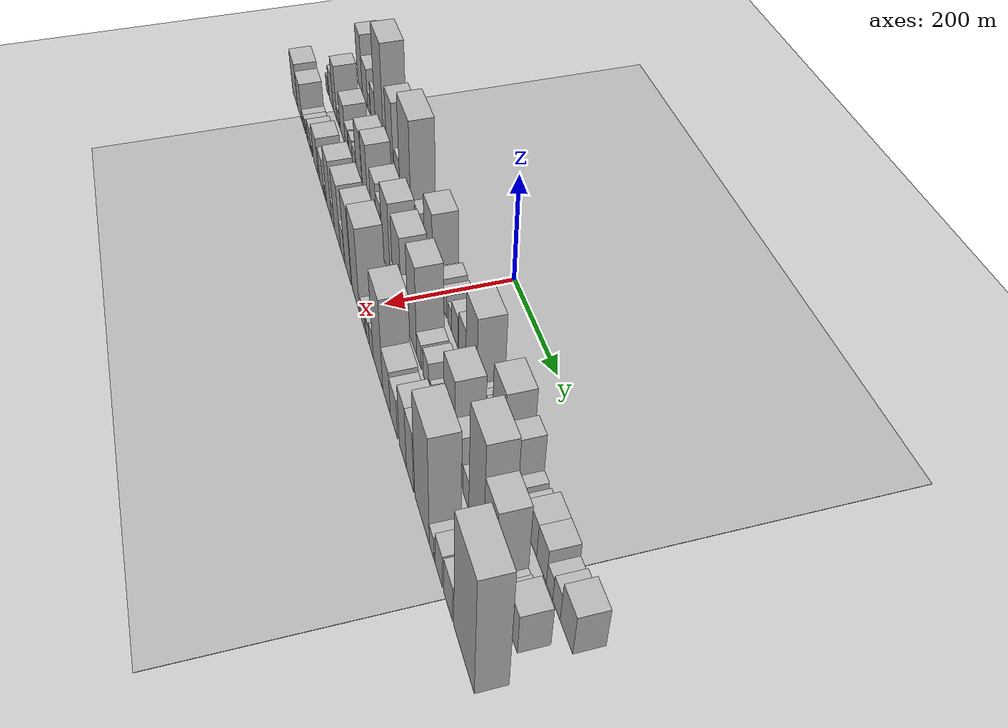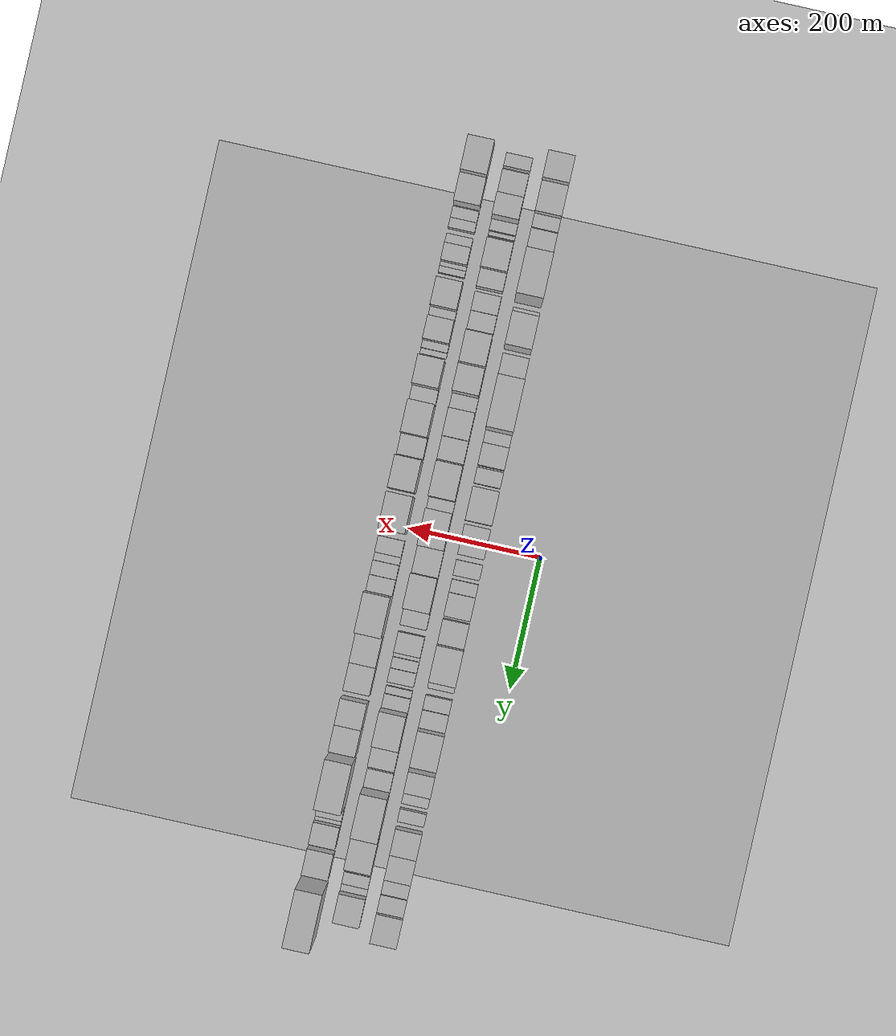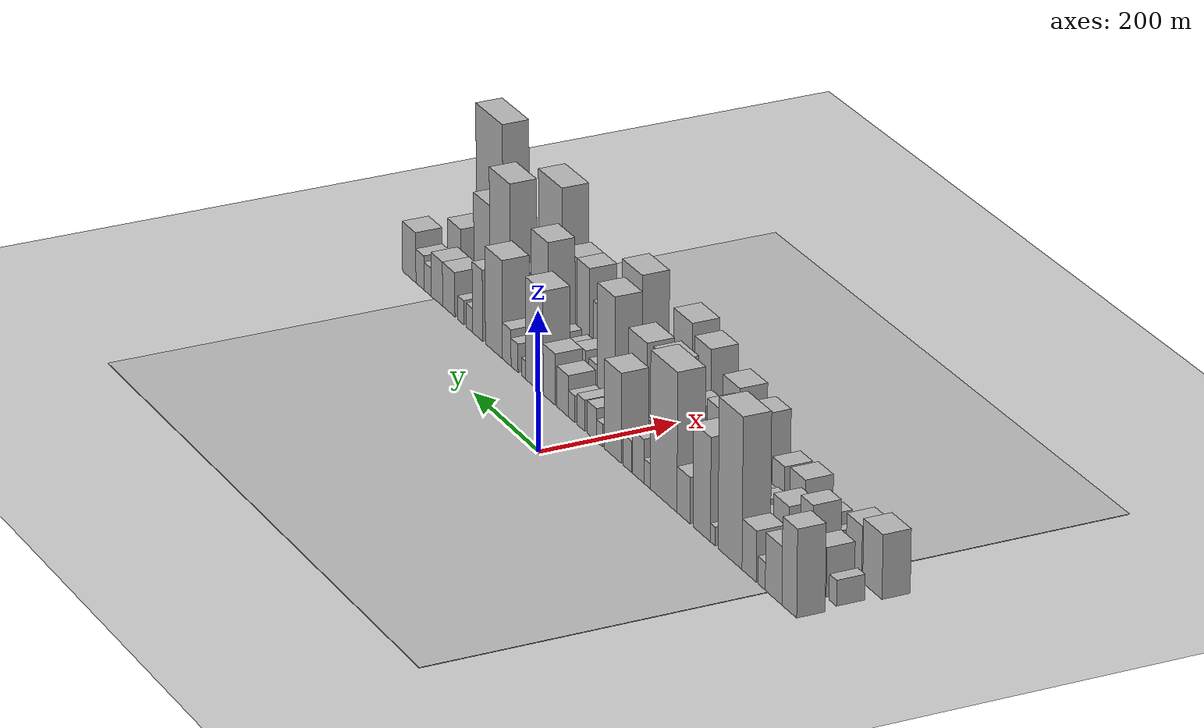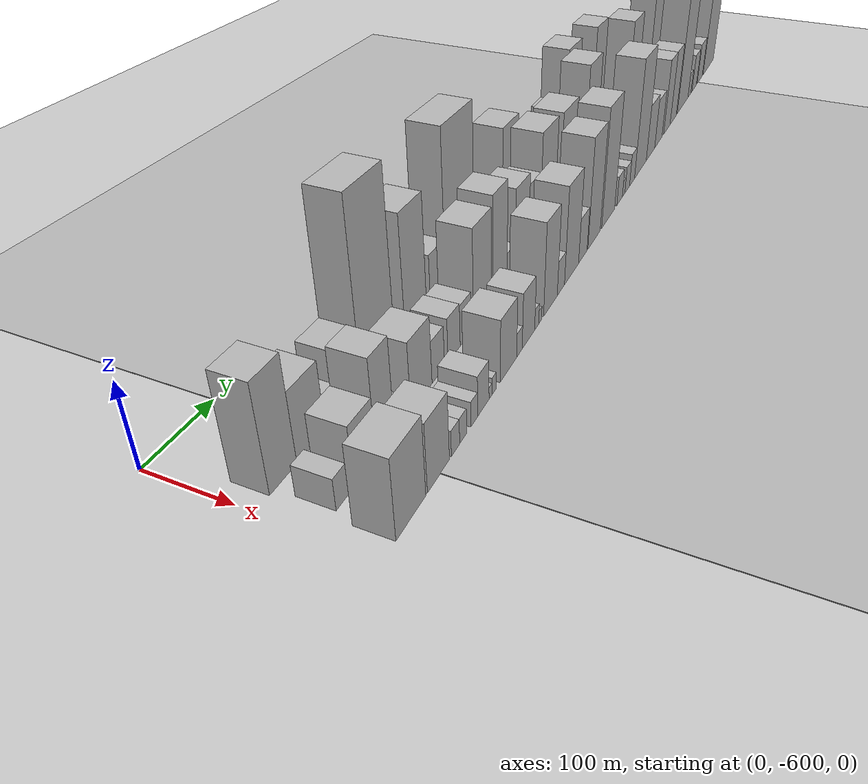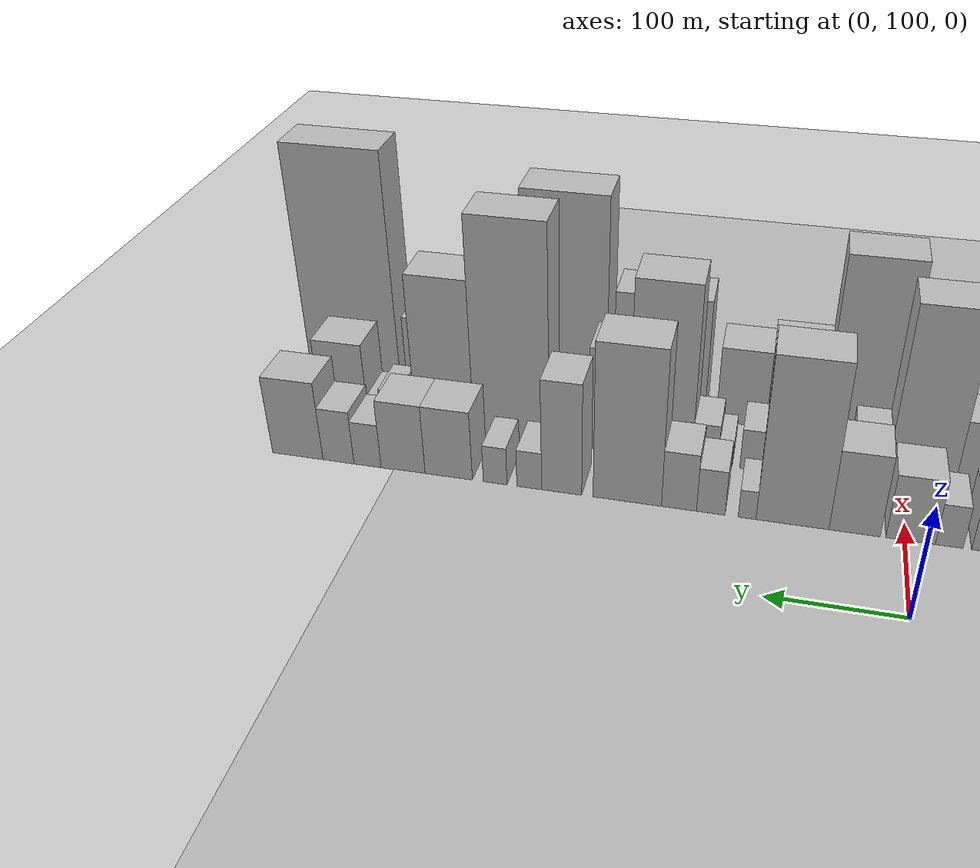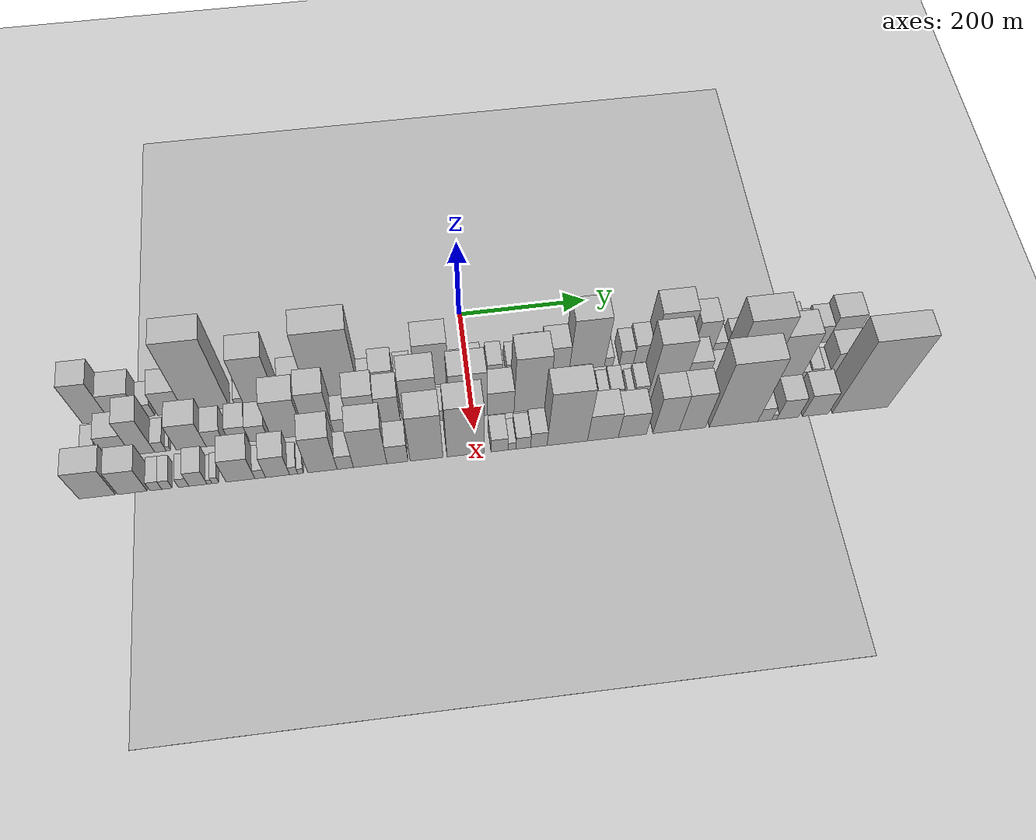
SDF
<?xml version="1.0" encoding="utf-8"?>

<sdf version="1.6">

   <world name="default">

      <gui fullscreen="0">

         <camera name="user_camera">

            <pose>-15 0 4.57585 0 0 0</pose>

            <view_controller>orbit</view_controller>

         </camera>

      </gui>

      <scene>

         <sky>

           <clouds>

             <speed>12</speed>

           </clouds>

         </sky>

         <ambient>0.4 0.4 0.4 1</ambient>

         <background>0.7 0.7 0.7 1</background>

         <shadows>1</shadows>

      </scene>

      <gravity>0 0 -9.8066</gravity>

      <magnetic_field>6e-06 2.3e-05 -4.2e-05</magnetic_field>

      <physics default="0" name="default_physics" type="ode">

         <ode>

            <solver>

               <type>quick</type>

               <iters>10</iters>

               <sor>1.0</sor>

               <use_dynamic_moi_rescaling>0</use_dynamic_moi_rescaling>

            </solver>

            <constraints>

               <cfm>0</cfm>

               <erp>0.2</erp>

               <contact_max_correcting_vel>100</contact_max_correcting_vel>

               <contact_surface_layer>0.001</contact_surface_layer>

            </constraints>

         </ode>

         <max_step_size>0.004</max_step_size>

         <real_time_factor>1</real_time_factor>

         <real_time_update_rate>250</real_time_update_rate>

      </physics>

      <light name="sun" type="directional">

         <cast_shadows>1</cast_shadows>

         <pose>0 0 10 0 0 0</pose>

         <diffuse>0.8 0.8 0.8 1</diffuse>

         <specular>0.2 0.2 0.2 1</specular>

         <attenuation>

            <range>1000</range>

            <constant>0.9</constant>

            <linear>0.01</linear>

            <quadratic>0.001</quadratic>

         </attenuation>

         <direction>-0.5 0.1 -0.9</direction>

      </light>

      <include>

         <name>ground_plane_1</name>

         <uri>model://HANNAS_ground_plane</uri>

         <pose>0 0 0  0 0 0</pose>

      </include>

      <include>

         <name>ground_plane_2</name>

         <uri>model://HANNAS_ground_plane</uri>

         <pose>100 0 0  0 0 0</pose>

      </include>

      <model name="building_1">

         <static>1</static>

         <pose frame="">100.0000 -559.7315 0 0.000000 0.000000 0.000000</pose>

         <link name="link">

            <pose frame="">0 0 61.50 0 0 0</pose>

            <collision name="collision">

               <geometry>

                  <box>

                     <size>40.0000 40.5371 123.0000</size>

                  </box>

               </geometry>

               <max_contacts>10</max_contacts>

               <surface>

                  <contact>

                     <ode/>

                  </contact>

                  <bounce/>

                  <friction>

                     <torsional>

                        <ode/>

                     </torsional>

                     <ode/>

                  </friction>

               </surface>

            </collision>

            <visual name="visual">

               <cast_shadows>0</cast_shadows>

               <geometry>

                  <box>

                     <size>40.0000 40.5371 123.0000</size>

                  </box>

               </geometry>

               <material>

                  <script>

                     <uri>model://HANNAS_wall/materials/scripts</uri>

                     <uri>model://HANNAS_wall/materials/textures</uri>

                     <name>vrc/HANNAS_wall</name>

                  </script>

               </material>

            </visual>

            <self_collide>0</self_collide>

            <enable_wind>0</enable_wind>

            <kinematic>0</kinematic>

         </link>

      </model>

      <model name="building_2">

         <static>1</static>

         <pose frame="">100.0000 -516.5617 0 0.000000 0.000000 0.000000</pose>

         <link name="link">

            <pose frame="">0 0 40.50 0 0 0</pose>

            <collision name="collision">

               <geometry>

                  <box>

                     <size>40.0000 45.8025 81.0000</size>

                  </box>

               </geometry>

               <max_contacts>10</max_contacts>

               <surface>

                  <contact>

                     <ode/>

                  </contact>

                  <bounce/>

                  <friction>

                     <torsional>

                        <ode/>

                     </torsional>

                     <ode/>

                  </friction>

               </surface>

            </collision>

            <visual name="visual">

               <cast_shadows>0</cast_shadows>

               <geometry>

                  <box>

                     <size>40.0000 45.8025 81.0000</size>

                  </box>

               </geometry>

               <material>

                  <script>

                     <uri>model://HANNAS_wall/materials/scripts</uri>

                     <uri>model://HANNAS_wall/materials/textures</uri>

                     <name>vrc/HANNAS_wall</name>

                  </script>

               </material>

            </visual>

            <self_collide>0</self_collide>

            <enable_wind>0</enable_wind>

            <kinematic>0</kinematic>

         </link>

      </model>

      <model name="building_3">

         <static>1</static>

         <pose frame="">100.0000 -483.2042 0 0.000000 0.000000 0.000000</pose>

         <link name="link">

            <pose frame="">0 0 19.50 0 0 0</pose>

            <collision name="collision">

               <geometry>

                  <box>

                     <size>40.0000 20.9124 39.0000</size>

                  </box>

               </geometry>

               <max_contacts>10</max_contacts>

               <surface>

                  <contact>

                     <ode/>

                  </contact>

                  <bounce/>

                  <friction>

                     <torsional>

                        <ode/>

                     </torsional>

                     <ode/>

                  </friction>

               </surface>

            </collision>

            <visual name="visual">

               <cast_shadows>0</cast_shadows>

               <geometry>

                  <box>

                     <size>40.0000 20.9124 39.0000</size>

                  </box>

               </geometry>

               <material>

                  <script>

                     <uri>model://HANNAS_wall/materials/scripts</uri>

                     <uri>model://HANNAS_wall/materials/textures</uri>

                     <name>vrc/HANNAS_wall</name>

                  </script>

               </material>

            </visual>

            <self_collide>0</self_collide>

            <enable_wind>0</enable_wind>

            <kinematic>0</kinematic>

         </link>

      </model>

      <model name="building_4">

         <static>1</static>

         <pose frame="">100.0000 -448.7653 0 0.000000 0.000000 0.000000</pose>

         <link name="link">

            <pose frame="">0 0 36.00 0 0 0</pose>

            <collision name="collision">

               <geometry>

                  <box>

                     <size>40.0000 39.9656 72.0000</size>

                  </box>

               </geometry>

               <max_contacts>10</max_contacts>

               <surface>

                  <contact>

                     <ode/>

                  </contact>

                  <bounce/>

                  <friction>

                     <torsional>

                        <ode/>

                     </torsional>

                     <ode/>

                  </friction>

               </surface>

            </collision>

            <visual name="visual">

               <cast_shadows>0</cast_shadows>

               <geometry>

                  <box>

                     <size>40.0000 39.9656 72.0000</size>

                  </box>

               </geometry>

               <material>

                  <script>

                     <uri>model://HANNAS_wall/materials/scripts</uri>

                     <uri>model://HANNAS_wall/materials/textures</uri>

                     <name>vrc/HANNAS_wall</name>

                  </script>

               </material>

            </visual>

            <self_collide>0</self_collide>

            <enable_wind>0</enable_wind>

            <kinematic>0</kinematic>

         </link>

      </model>

      <model name="building_5">

         <static>1</static>

         <pose frame="">100.0000 -395.1472 0 0.000000 0.000000 0.000000</pose>

         <link name="link">

            <pose frame="">0 0 106.50 0 0 0</pose>

            <collision name="collision">

               <geometry>

                  <box>

                     <size>40.0000 67.2705 213.0000</size>

                  </box>

               </geometry>

               <max_contacts>10</max_contacts>

               <surface>

                  <contact>

                     <ode/>

                  </contact>

                  <bounce/>

                  <friction>

                     <torsional>

                        <ode/>

                     </torsional>

                     <ode/>

                  </friction>

               </surface>

            </collision>

            <visual name="visual">

               <cast_shadows>0</cast_shadows>

               <geometry>

                  <box>

                     <size>40.0000 67.2705 213.0000</size>

                  </box>

               </geometry>

               <material>

                  <script>

                     <uri>model://HANNAS_wall/materials/scripts</uri>

                     <uri>model://HANNAS_wall/materials/textures</uri>

                     <name>vrc/HANNAS_wall</name>

                  </script>

               </material>

            </visual>

            <self_collide>0</self_collide>

            <enable_wind>0</enable_wind>

            <kinematic>0</kinematic>

         </link>

      </model>

      <model name="building_6">

         <static>1</static>

         <pose frame="">100.0000 -346.0317 0 0.000000 0.000000 0.000000</pose>

         <link name="link">

            <pose frame="">0 0 13.50 0 0 0</pose>

            <collision name="collision">

               <geometry>

                  <box>

                     <size>40.0000 12.9604 27.0000</size>

                  </box>

               </geometry>

               <max_contacts>10</max_contacts>

               <surface>

                  <contact>

                     <ode/>

                  </contact>

                  <bounce/>

                  <friction>

                     <torsional>

                        <ode/>

                     </torsional>

                     <ode/>

                  </friction>

               </surface>

            </collision>

            <visual name="visual">

               <cast_shadows>0</cast_shadows>

               <geometry>

                  <box>

                     <size>40.0000 12.9604 27.0000</size>

                  </box>

               </geometry>

               <material>

                  <script>

                     <uri>model://HANNAS_wall/materials/scripts</uri>

                     <uri>model://HANNAS_wall/materials/textures</uri>

                     <name>vrc/HANNAS_wall</name>

                  </script>

               </material>

            </visual>

            <self_collide>0</self_collide>

            <enable_wind>0</enable_wind>

            <kinematic>0</kinematic>

         </link>

      </model>

      <model name="building_7">

         <static>1</static>

         <pose frame="">100.0000 -314.8687 0 0.000000 0.000000 0.000000</pose>

         <link name="link">

            <pose frame="">0 0 73.50 0 0 0</pose>

            <collision name="collision">

               <geometry>

                  <box>

                     <size>40.0000 49.3657 147.0000</size>

                  </box>

               </geometry>

               <max_contacts>10</max_contacts>

               <surface>

                  <contact>

                     <ode/>

                  </contact>

                  <bounce/>

                  <friction>

                     <torsional>

                        <ode/>

                     </torsional>

                     <ode/>

                  </friction>

               </surface>

            </collision>

            <visual name="visual">

               <cast_shadows>0</cast_shadows>

               <geometry>

                  <box>

                     <size>40.0000 49.3657 147.0000</size>

                  </box>

               </geometry>

               <material>

                  <script>

                     <uri>model://HANNAS_wall/materials/scripts</uri>

                     <uri>model://HANNAS_wall/materials/textures</uri>

                     <name>vrc/HANNAS_wall</name>

                  </script>

               </material>

            </visual>

            <self_collide>0</self_collide>

            <enable_wind>0</enable_wind>

            <kinematic>0</kinematic>

         </link>

      </model>

      <model name="building_8">

         <static>1</static>

         <pose frame="">100.0000 -262.5268 0 0.000000 0.000000 0.000000</pose>

         <link name="link">

            <pose frame="">0 0 33.00 0 0 0</pose>

            <collision name="collision">

               <geometry>

                  <box>

                     <size>40.0000 37.3182 66.0000</size>

                  </box>

               </geometry>

               <max_contacts>10</max_contacts>

               <surface>

                  <contact>

                     <ode/>

                  </contact>

                  <bounce/>

                  <friction>

                     <torsional>

                        <ode/>

                     </torsional>

                     <ode/>

                  </friction>

               </surface>

            </collision>

            <visual name="visual">

               <cast_shadows>0</cast_shadows>

               <geometry>

                  <box>

                     <size>40.0000 37.3182 66.0000</size>

                  </box>

               </geometry>

               <material>

                  <script>

                     <uri>model://HANNAS_wall/materials/scripts</uri>

                     <uri>model://HANNAS_wall/materials/textures</uri>

                     <name>vrc/HANNAS_wall</name>

                  </script>

               </material>

            </visual>

            <self_collide>0</self_collide>

            <enable_wind>0</enable_wind>

            <kinematic>0</kinematic>

         </link>

      </model>

      <model name="building_9">

         <static>1</static>

         <pose frame="">100.0000 -205.1565 0 0.000000 0.000000 0.000000</pose>

         <link name="link">

            <pose frame="">0 0 99.00 0 0 0</pose>

            <collision name="collision">

               <geometry>

                  <box>

                     <size>40.0000 77.4223 198.0000</size>

                  </box>

               </geometry>

               <max_contacts>10</max_contacts>

               <surface>

                  <contact>

                     <ode/>

                  </contact>

                  <bounce/>

                  <friction>

                     <torsional>

                        <ode/>

                     </torsional>

                     <ode/>

                  </friction>

               </surface>

            </collision>

            <visual name="visual">

               <cast_shadows>0</cast_shadows>

               <geometry>

                  <box>

                     <size>40.0000 77.4223 198.0000</size>

                  </box>

               </geometry>

               <material>

                  <script>

                     <uri>model://HANNAS_wall/materials/scripts</uri>

                     <uri>model://HANNAS_wall/materials/textures</uri>

                     <name>vrc/HANNAS_wall</name>

                  </script>

               </material>

            </visual>

            <self_collide>0</self_collide>

            <enable_wind>0</enable_wind>

            <kinematic>0</kinematic>

         </link>

      </model>

      <model name="building_10">

         <static>1</static>

         <pose frame="">100.0000 -156.7581 0 0.000000 0.000000 0.000000</pose>

         <link name="link">

            <pose frame="">0 0 18.00 0 0 0</pose>

            <collision name="collision">

               <geometry>

                  <box>

                     <size>40.0000 19.3747 36.0000</size>

                  </box>

               </geometry>

               <max_contacts>10</max_contacts>

               <surface>

                  <contact>

                     <ode/>

                  </contact>

                  <bounce/>

                  <friction>

                     <torsional>

                        <ode/>

                     </torsional>

                     <ode/>

                  </friction>

               </surface>

            </collision>

            <visual name="visual">

               <cast_shadows>0</cast_shadows>

               <geometry>

                  <box>

                     <size>40.0000 19.3747 36.0000</size>

                  </box>

               </geometry>

               <material>

                  <script>

                     <uri>model://HANNAS_wall/materials/scripts</uri>

                     <uri>model://HANNAS_wall/materials/textures</uri>

                     <name>vrc/HANNAS_wall</name>

                  </script>

               </material>

            </visual>

            <self_collide>0</self_collide>

            <enable_wind>0</enable_wind>

            <kinematic>0</kinematic>

         </link>

      </model>

      <model name="building_11">

         <static>1</static>

         <pose frame="">100.0000 -130.1553 0 0.000000 0.000000 0.000000</pose>

         <link name="link">

            <pose frame="">0 0 31.50 0 0 0</pose>

            <collision name="collision">

               <geometry>

                  <box>

                     <size>40.0000 33.8308 63.0000</size>

                  </box>

               </geometry>

               <max_contacts>10</max_contacts>

               <surface>

                  <contact>

                     <ode/>

                  </contact>

                  <bounce/>

                  <friction>

                     <torsional>

                        <ode/>

                     </torsional>

                     <ode/>

                  </friction>

               </surface>

            </collision>

            <visual name="visual">

               <cast_shadows>0</cast_shadows>

               <geometry>

                  <box>

                     <size>40.0000 33.8308 63.0000</size>

                  </box>

               </geometry>

               <material>

                  <script>

                     <uri>model://HANNAS_wall/materials/scripts</uri>

                     <uri>model://HANNAS_wall/materials/textures</uri>

                     <name>vrc/HANNAS_wall</name>

                  </script>

               </material>

            </visual>

            <self_collide>0</self_collide>

            <enable_wind>0</enable_wind>

            <kinematic>0</kinematic>

         </link>

      </model>

      <model name="building_12">

         <static>1</static>

         <pose frame="">100.0000 -98.2092 0 0.000000 0.000000 0.000000</pose>

         <link name="link">

            <pose frame="">0 0 22.50 0 0 0</pose>

            <collision name="collision">

               <geometry>

                  <box>

                     <size>40.0000 24.0616 45.0000</size>

                  </box>

               </geometry>

               <max_contacts>10</max_contacts>

               <surface>

                  <contact>

                     <ode/>

                  </contact>

                  <bounce/>

                  <friction>

                     <torsional>

                        <ode/>

                     </torsional>

                     <ode/>

                  </friction>

               </surface>

            </collision>

            <visual name="visual">

               <cast_shadows>0</cast_shadows>

               <geometry>

                  <box>

                     <size>40.0000 24.0616 45.0000</size>

                  </box>

               </geometry>

               <material>

                  <script>

                     <uri>model://HANNAS_wall/materials/scripts</uri>

                     <uri>model://HANNAS_wall/materials/textures</uri>

                     <name>vrc/HANNAS_wall</name>

                  </script>

               </material>

            </visual>

            <self_collide>0</self_collide>

            <enable_wind>0</enable_wind>

            <kinematic>0</kinematic>

         </link>

      </model>

      <model name="building_13">

         <static>1</static>

         <pose frame="">100.0000 -54.8685 0 0.000000 0.000000 0.000000</pose>

         <link name="link">

            <pose frame="">0 0 64.50 0 0 0</pose>

            <collision name="collision">

               <geometry>

                  <box>

                     <size>40.0000 50.6198 129.0000</size>

                  </box>

               </geometry>

               <max_contacts>10</max_contacts>

               <surface>

                  <contact>

                     <ode/>

                  </contact>

                  <bounce/>

                  <friction>

                     <torsional>

                        <ode/>

                     </torsional>

                     <ode/>

                  </friction>

               </surface>

            </collision>

            <visual name="visual">

               <cast_shadows>0</cast_shadows>

               <geometry>

                  <box>

                     <size>40.0000 50.6198 129.0000</size>

                  </box>

               </geometry>

               <material>

                  <script>

                     <uri>model://HANNAS_wall/materials/scripts</uri>

                     <uri>model://HANNAS_wall/materials/textures</uri>

                     <name>vrc/HANNAS_wall</name>

                  </script>

               </material>

            </visual>

            <self_collide>0</self_collide>

            <enable_wind>0</enable_wind>

            <kinematic>0</kinematic>

         </link>

      </model>

      <model name="building_14">

         <static>1</static>

         <pose frame="">100.0000 -15.6420 0 0.000000 0.000000 0.000000</pose>

         <link name="link">

            <pose frame="">0 0 16.50 0 0 0</pose>

            <collision name="collision">

               <geometry>

                  <box>

                     <size>40.0000 17.8331 33.0000</size>

                  </box>

               </geometry>

               <max_contacts>10</max_contacts>

               <surface>

                  <contact>

                     <ode/>

                  </contact>

                  <bounce/>

                  <friction>

                     <torsional>

                        <ode/>

                     </torsional>

                     <ode/>

                  </friction>

               </surface>

            </collision>

            <visual name="visual">

               <cast_shadows>0</cast_shadows>

               <geometry>

                  <box>

                     <size>40.0000 17.8331 33.0000</size>

                  </box>

               </geometry>

               <material>

                  <script>

                     <uri>model://HANNAS_wall/materials/scripts</uri>

                     <uri>model://HANNAS_wall/materials/textures</uri>

                     <name>vrc/HANNAS_wall</name>

                  </script>

               </material>

            </visual>

            <self_collide>0</self_collide>

            <enable_wind>0</enable_wind>

            <kinematic>0</kinematic>

         </link>

      </model>

      <model name="building_15">

         <static>1</static>

         <pose frame="">100.0000 7.3285 0 0.000000 0.000000 0.000000</pose>

         <link name="link">

            <pose frame="">0 0 24.00 0 0 0</pose>

            <collision name="collision">

               <geometry>

                  <box>

                     <size>40.0000 28.1079 48.0000</size>

                  </box>

               </geometry>

               <max_contacts>10</max_contacts>

               <surface>

                  <contact>

                     <ode/>

                  </contact>

                  <bounce/>

                  <friction>

                     <torsional>

                        <ode/>

                     </torsional>

                     <ode/>

                  </friction>

               </surface>

            </collision>

            <visual name="visual">

               <cast_shadows>0</cast_shadows>

               <geometry>

                  <box>

                     <size>40.0000 28.1079 48.0000</size>

                  </box>

               </geometry>

               <material>

                  <script>

                     <uri>model://HANNAS_wall/materials/scripts</uri>

                     <uri>model://HANNAS_wall/materials/textures</uri>

                     <name>vrc/HANNAS_wall</name>

                  </script>

               </material>

            </visual>

            <self_collide>0</self_collide>

            <enable_wind>0</enable_wind>

            <kinematic>0</kinematic>

         </link>

      </model>

      <model name="building_16">

         <static>1</static>

         <pose frame="">100.0000 41.1134 0 0.000000 0.000000 0.000000</pose>

         <link name="link">

            <pose frame="">0 0 22.50 0 0 0</pose>

            <collision name="collision">

               <geometry>

                  <box>

                     <size>40.0000 23.4620 45.0000</size>

                  </box>

               </geometry>

               <max_contacts>10</max_contacts>

               <surface>

                  <contact>

                     <ode/>

                  </contact>

                  <bounce/>

                  <friction>

                     <torsional>

                        <ode/>

                     </torsional>

                     <ode/>

                  </friction>

               </surface>

            </collision>

            <visual name="visual">

               <cast_shadows>0</cast_shadows>

               <geometry>

                  <box>

                     <size>40.0000 23.4620 45.0000</size>

                  </box>

               </geometry>

               <material>

                  <script>

                     <uri>model://HANNAS_wall/materials/scripts</uri>

                     <uri>model://HANNAS_wall/materials/textures</uri>

                     <name>vrc/HANNAS_wall</name>

                  </script>

               </material>

            </visual>

            <self_collide>0</self_collide>

            <enable_wind>0</enable_wind>

            <kinematic>0</kinematic>

         </link>

      </model>

      <model name="building_17">

         <static>1</static>

         <pose frame="">100.0000 68.7270 0 0.000000 0.000000 0.000000</pose>

         <link name="link">

            <pose frame="">0 0 19.50 0 0 0</pose>

            <collision name="collision">

               <geometry>

                  <box>

                     <size>40.0000 19.7653 39.0000</size>

                  </box>

               </geometry>

               <max_contacts>10</max_contacts>

               <surface>

                  <contact>

                     <ode/>

                  </contact>

                  <bounce/>

                  <friction>

                     <torsional>

                        <ode/>

                     </torsional>

                     <ode/>

                  </friction>

               </surface>

            </collision>

            <visual name="visual">

               <cast_shadows>0</cast_shadows>

               <geometry>

                  <box>

                     <size>40.0000 19.7653 39.0000</size>

                  </box>

               </geometry>

               <material>

                  <script>

                     <uri>model://HANNAS_wall/materials/scripts</uri>

                     <uri>model://HANNAS_wall/materials/textures</uri>

                     <name>vrc/HANNAS_wall</name>

                  </script>

               </material>

            </visual>

            <self_collide>0</self_collide>

            <enable_wind>0</enable_wind>

            <kinematic>0</kinematic>

         </link>

      </model>

      <model name="building_18">

         <static>1</static>

         <pose frame="">100.0000 96.4455 0 0.000000 0.000000 0.000000</pose>

         <link name="link">

            <pose frame="">0 0 30.00 0 0 0</pose>

            <collision name="collision">

               <geometry>

                  <box>

                     <size>40.0000 35.6717 60.0000</size>

                  </box>

               </geometry>

               <max_contacts>10</max_contacts>

               <surface>

                  <contact>

                     <ode/>

                  </contact>

                  <bounce/>

                  <friction>

                     <torsional>

                        <ode/>

                     </torsional>

                     <ode/>

                  </friction>

               </surface>

            </collision>

            <visual name="visual">

               <cast_shadows>0</cast_shadows>

               <geometry>

                  <box>

                     <size>40.0000 35.6717 60.0000</size>

                  </box>

               </geometry>

               <material>

                  <script>

                     <uri>model://HANNAS_wall/materials/scripts</uri>

                     <uri>model://HANNAS_wall/materials/textures</uri>

                     <name>vrc/HANNAS_wall</name>

                  </script>

               </material>

            </visual>

            <self_collide>0</self_collide>

            <enable_wind>0</enable_wind>

            <kinematic>0</kinematic>

         </link>

      </model>

      <model name="building_19">

         <static>1</static>

         <pose frame="">100.0000 137.0450 0 0.000000 0.000000 0.000000</pose>

         <link name="link">

            <pose frame="">0 0 37.50 0 0 0</pose>

            <collision name="collision">

               <geometry>

                  <box>

                     <size>40.0000 37.5273 75.0000</size>

                  </box>

               </geometry>

               <max_contacts>10</max_contacts>

               <surface>

                  <contact>

                     <ode/>

                  </contact>

                  <bounce/>

                  <friction>

                     <torsional>

                        <ode/>

                     </torsional>

                     <ode/>

                  </friction>

               </surface>

            </collision>

            <visual name="visual">

               <cast_shadows>0</cast_shadows>

               <geometry>

                  <box>

                     <size>40.0000 37.5273 75.0000</size>

                  </box>

               </geometry>

               <material>

                  <script>

                     <uri>model://HANNAS_wall/materials/scripts</uri>

                     <uri>model://HANNAS_wall/materials/textures</uri>

                     <name>vrc/HANNAS_wall</name>

                  </script>

               </material>

            </visual>

            <self_collide>0</self_collide>

            <enable_wind>0</enable_wind>

            <kinematic>0</kinematic>

         </link>

      </model>

      <model name="building_20">

         <static>1</static>

         <pose frame="">100.0000 183.0743 0 0.000000 0.000000 0.000000</pose>

         <link name="link">

            <pose frame="">0 0 75.00 0 0 0</pose>

            <collision name="collision">

               <geometry>

                  <box>

                     <size>40.0000 54.5314 150.0000</size>

                  </box>

               </geometry>

               <max_contacts>10</max_contacts>

               <surface>

                  <contact>

                     <ode/>

                  </contact>

                  <bounce/>

                  <friction>

                     <torsional>

                        <ode/>

                     </torsional>

                     <ode/>

                  </friction>

               </surface>

            </collision>

            <visual name="visual">

               <cast_shadows>0</cast_shadows>

               <geometry>

                  <box>

                     <size>40.0000 54.5314 150.0000</size>

                  </box>

               </geometry>

               <material>

                  <script>

                     <uri>model://HANNAS_wall/materials/scripts</uri>

                     <uri>model://HANNAS_wall/materials/textures</uri>

                     <name>vrc/HANNAS_wall</name>

                  </script>

               </material>

            </visual>

            <self_collide>0</self_collide>

            <enable_wind>0</enable_wind>

            <kinematic>0</kinematic>

         </link>

      </model>

      <model name="building_21">

         <static>1</static>

         <pose frame="">100.0000 217.0555 0 0.000000 0.000000 0.000000</pose>

         <link name="link">

            <pose frame="">0 0 13.50 0 0 0</pose>

            <collision name="collision">

               <geometry>

                  <box>

                     <size>40.0000 13.4309 27.0000</size>

                  </box>

               </geometry>

               <max_contacts>10</max_contacts>

               <surface>

                  <contact>

                     <ode/>

                  </contact>

                  <bounce/>

                  <friction>

                     <torsional>

                        <ode/>

                     </torsional>

                     <ode/>

                  </friction>

               </surface>

            </collision>

            <visual name="visual">

               <cast_shadows>0</cast_shadows>

               <geometry>

                  <box>

                     <size>40.0000 13.4309 27.0000</size>

                  </box>

               </geometry>

               <material>

                  <script>

                     <uri>model://HANNAS_wall/materials/scripts</uri>

                     <uri>model://HANNAS_wall/materials/textures</uri>

                     <name>vrc/HANNAS_wall</name>

                  </script>

               </material>

            </visual>

            <self_collide>0</self_collide>

            <enable_wind>0</enable_wind>

            <kinematic>0</kinematic>

         </link>

      </model>

      <model name="building_22">

         <static>1</static>

         <pose frame="">100.0000 244.7112 0 0.000000 0.000000 0.000000</pose>

         <link name="link">

            <pose frame="">0 0 21.00 0 0 0</pose>

            <collision name="collision">

               <geometry>

                  <box>

                     <size>40.0000 21.8806 42.0000</size>

                  </box>

               </geometry>

               <max_contacts>10</max_contacts>

               <surface>

                  <contact>

                     <ode/>

                  </contact>

                  <bounce/>

                  <friction>

                     <torsional>

                        <ode/>

                     </torsional>

                     <ode/>

                  </friction>

               </surface>

            </collision>

            <visual name="visual">

               <cast_shadows>0</cast_shadows>

               <geometry>

                  <box>

                     <size>40.0000 21.8806 42.0000</size>

                  </box>

               </geometry>

               <material>

                  <script>

                     <uri>model://HANNAS_wall/materials/scripts</uri>

                     <uri>model://HANNAS_wall/materials/textures</uri>

                     <name>vrc/HANNAS_wall</name>

                  </script>

               </material>

            </visual>

            <self_collide>0</self_collide>

            <enable_wind>0</enable_wind>

            <kinematic>0</kinematic>

         </link>

      </model>

      <model name="building_23">

         <static>1</static>

         <pose frame="">100.0000 269.1983 0 0.000000 0.000000 0.000000</pose>

         <link name="link">

            <pose frame="">0 0 27.00 0 0 0</pose>

            <collision name="collision">

               <geometry>

                  <box>

                     <size>40.0000 27.0935 54.0000</size>

                  </box>

               </geometry>

               <max_contacts>10</max_contacts>

               <surface>

                  <contact>

                     <ode/>

                  </contact>

                  <bounce/>

                  <friction>

                     <torsional>

                        <ode/>

                     </torsional>

                     <ode/>

                  </friction>

               </surface>

            </collision>

            <visual name="visual">

               <cast_shadows>0</cast_shadows>

               <geometry>

                  <box>

                     <size>40.0000 27.0935 54.0000</size>

                  </box>

               </geometry>

               <material>

                  <script>

                     <uri>model://HANNAS_wall/materials/scripts</uri>

                     <uri>model://HANNAS_wall/materials/textures</uri>

                     <name>vrc/HANNAS_wall</name>

                  </script>

               </material>

            </visual>

            <self_collide>0</self_collide>

            <enable_wind>0</enable_wind>

            <kinematic>0</kinematic>

         </link>

      </model>

      <model name="building_24">

         <static>1</static>

         <pose frame="">100.0000 309.6436 0 0.000000 0.000000 0.000000</pose>

         <link name="link">

            <pose frame="">0 0 72.00 0 0 0</pose>

            <collision name="collision">

               <geometry>

                  <box>

                     <size>40.0000 53.7971 144.0000</size>

                  </box>

               </geometry>

               <max_contacts>10</max_contacts>

               <surface>

                  <contact>

                     <ode/>

                  </contact>

                  <bounce/>

                  <friction>

                     <torsional>

                        <ode/>

                     </torsional>

                     <ode/>

                  </friction>

               </surface>

            </collision>

            <visual name="visual">

               <cast_shadows>0</cast_shadows>

               <geometry>

                  <box>

                     <size>40.0000 53.7971 144.0000</size>

                  </box>

               </geometry>

               <material>

                  <script>

                     <uri>model://HANNAS_wall/materials/scripts</uri>

                     <uri>model://HANNAS_wall/materials/textures</uri>

                     <name>vrc/HANNAS_wall</name>

                  </script>

               </material>

            </visual>

            <self_collide>0</self_collide>

            <enable_wind>0</enable_wind>

            <kinematic>0</kinematic>

         </link>

      </model>

      <model name="building_25">

         <static>1</static>

         <pose frame="">100.0000 361.6210 0 0.000000 0.000000 0.000000</pose>

         <link name="link">

            <pose frame="">0 0 52.50 0 0 0</pose>

            <collision name="collision">

               <geometry>

                  <box>

                     <size>40.0000 32.1577 105.0000</size>

                  </box>

               </geometry>

               <max_contacts>10</max_contacts>

               <surface>

                  <contact>

                     <ode/>

                  </contact>

                  <bounce/>

                  <friction>

                     <torsional>

                        <ode/>

                     </torsional>

                     <ode/>

                  </friction>

               </surface>

            </collision>

            <visual name="visual">

               <cast_shadows>0</cast_shadows>

               <geometry>

                  <box>

                     <size>40.0000 32.1577 105.0000</size>

                  </box>

               </geometry>

               <material>

                  <script>

                     <uri>model://HANNAS_wall/materials/scripts</uri>

                     <uri>model://HANNAS_wall/materials/textures</uri>

                     <name>vrc/HANNAS_wall</name>

                  </script>

               </material>

            </visual>

            <self_collide>0</self_collide>

            <enable_wind>0</enable_wind>

            <kinematic>0</kinematic>

         </link>

      </model>

      <model name="building_26">

         <static>1</static>

         <pose frame="">100.0000 387.7952 0 0.000000 0.000000 0.000000</pose>

         <link name="link">

            <pose frame="">0 0 18.00 0 0 0</pose>

            <collision name="collision">

               <geometry>

                  <box>

                     <size>40.0000 20.1906 36.0000</size>

                  </box>

               </geometry>

               <max_contacts>10</max_contacts>

               <surface>

                  <contact>

                     <ode/>

                  </contact>

                  <bounce/>

                  <friction>

                     <torsional>

                        <ode/>

                     </torsional>

                     <ode/>

                  </friction>

               </surface>

            </collision>

            <visual name="visual">

               <cast_shadows>0</cast_shadows>

               <geometry>

                  <box>

                     <size>40.0000 20.1906 36.0000</size>

                  </box>

               </geometry>

               <material>

                  <script>

                     <uri>model://HANNAS_wall/materials/scripts</uri>

                     <uri>model://HANNAS_wall/materials/textures</uri>

                     <name>vrc/HANNAS_wall</name>

                  </script>

               </material>

            </visual>

            <self_collide>0</self_collide>

            <enable_wind>0</enable_wind>

            <kinematic>0</kinematic>

         </link>

      </model>

      <model name="building_27">

         <static>1</static>

         <pose frame="">100.0000 415.6163 0 0.000000 0.000000 0.000000</pose>

         <link name="link">

            <pose frame="">0 0 18.00 0 0 0</pose>

            <collision name="collision">

               <geometry>

                  <box>

                     <size>40.0000 19.4518 36.0000</size>

                  </box>

               </geometry>

               <max_contacts>10</max_contacts>

               <surface>

                  <contact>

                     <ode/>

                  </contact>

                  <bounce/>

                  <friction>

                     <torsional>

                        <ode/>

                     </torsional>

                     <ode/>

                  </friction>

               </surface>

            </collision>

            <visual name="visual">

               <cast_shadows>0</cast_shadows>

               <geometry>

                  <box>

                     <size>40.0000 19.4518 36.0000</size>

                  </box>

               </geometry>

               <material>

                  <script>

                     <uri>model://HANNAS_wall/materials/scripts</uri>

                     <uri>model://HANNAS_wall/materials/textures</uri>

                     <name>vrc/HANNAS_wall</name>

                  </script>

               </material>

            </visual>

            <self_collide>0</self_collide>

            <enable_wind>0</enable_wind>

            <kinematic>0</kinematic>

         </link>

      </model>

      <model name="building_28">

         <static>1</static>

         <pose frame="">100.0000 454.0794 0 0.000000 0.000000 0.000000</pose>

         <link name="link">

            <pose frame="">0 0 33.00 0 0 0</pose>

            <collision name="collision">

               <geometry>

                  <box>

                     <size>40.0000 39.4744 66.0000</size>

                  </box>

               </geometry>

               <max_contacts>10</max_contacts>

               <surface>

                  <contact>

                     <ode/>

                  </contact>

                  <bounce/>

                  <friction>

                     <torsional>

                        <ode/>

                     </torsional>

                     <ode/>

                  </friction>

               </surface>

            </collision>

            <visual name="visual">

               <cast_shadows>0</cast_shadows>

               <geometry>

                  <box>

                     <size>40.0000 39.4744 66.0000</size>

                  </box>

               </geometry>

               <material>

                  <script>

                     <uri>model://HANNAS_wall/materials/scripts</uri>

                     <uri>model://HANNAS_wall/materials/textures</uri>

                     <name>vrc/HANNAS_wall</name>

                  </script>

               </material>

            </visual>

            <self_collide>0</self_collide>

            <enable_wind>0</enable_wind>

            <kinematic>0</kinematic>

         </link>

      </model>

      <model name="building_29">

         <static>1</static>

         <pose frame="">100.0000 492.4047 0 0.000000 0.000000 0.000000</pose>

         <link name="link">

            <pose frame="">0 0 33.00 0 0 0</pose>

            <collision name="collision">

               <geometry>

                  <box>

                     <size>40.0000 37.1762 66.0000</size>

                  </box>

               </geometry>

               <max_contacts>10</max_contacts>

               <surface>

                  <contact>

                     <ode/>

                  </contact>

                  <bounce/>

                  <friction>

                     <torsional>

                        <ode/>

                     </torsional>

                     <ode/>

                  </friction>

               </surface>

            </collision>

            <visual name="visual">

               <cast_shadows>0</cast_shadows>

               <geometry>

                  <box>

                     <size>40.0000 37.1762 66.0000</size>

                  </box>

               </geometry>

               <material>

                  <script>

                     <uri>model://HANNAS_wall/materials/scripts</uri>

                     <uri>model://HANNAS_wall/materials/textures</uri>

                     <name>vrc/HANNAS_wall</name>

                  </script>

               </material>

            </visual>

            <self_collide>0</self_collide>

            <enable_wind>0</enable_wind>

            <kinematic>0</kinematic>

         </link>

      </model>

      <model name="building_30">

         <static>1</static>

         <pose frame="">100.0000 522.6397 0 0.000000 0.000000 0.000000</pose>

         <link name="link">

            <pose frame="">0 0 21.00 0 0 0</pose>

            <collision name="collision">

               <geometry>

                  <box>

                     <size>40.0000 23.2936 42.0000</size>

                  </box>

               </geometry>

               <max_contacts>10</max_contacts>

               <surface>

                  <contact>

                     <ode/>

                  </contact>

                  <bounce/>

                  <friction>

                     <torsional>

                        <ode/>

                     </torsional>

                     <ode/>

                  </friction>

               </surface>

            </collision>

            <visual name="visual">

               <cast_shadows>0</cast_shadows>

               <geometry>

                  <box>

                     <size>40.0000 23.2936 42.0000</size>

                  </box>

               </geometry>

               <material>

                  <script>

                     <uri>model://HANNAS_wall/materials/scripts</uri>

                     <uri>model://HANNAS_wall/materials/textures</uri>

                     <name>vrc/HANNAS_wall</name>

                  </script>

               </material>

            </visual>

            <self_collide>0</self_collide>

            <enable_wind>0</enable_wind>

            <kinematic>0</kinematic>

         </link>

      </model>

      <model name="building_31">

         <static>1</static>

         <pose frame="">100.0000 547.7002 0 0.000000 0.000000 0.000000</pose>

         <link name="link">

            <pose frame="">0 0 25.50 0 0 0</pose>

            <collision name="collision">

               <geometry>

                  <box>

                     <size>40.0000 26.8274 51.0000</size>

                  </box>

               </geometry>

               <max_contacts>10</max_contacts>

               <surface>

                  <contact>

                     <ode/>

                  </contact>

                  <bounce/>

                  <friction>

                     <torsional>

                        <ode/>

                     </torsional>

                     <ode/>

                  </friction>

               </surface>

            </collision>

            <visual name="visual">

               <cast_shadows>0</cast_shadows>

               <geometry>

                  <box>

                     <size>40.0000 26.8274 51.0000</size>

                  </box>

               </geometry>

               <material>

                  <script>

                     <uri>model://HANNAS_wall/materials/scripts</uri>

                     <uri>model://HANNAS_wall/materials/textures</uri>

                     <name>vrc/HANNAS_wall</name>

                  </script>

               </material>

            </visual>

            <self_collide>0</self_collide>

            <enable_wind>0</enable_wind>

            <kinematic>0</kinematic>

         </link>

      </model>

      <model name="building_32">

         <static>1</static>

         <pose frame="">100.0000 583.1854 0 0.000000 0.000000 0.000000</pose>

         <link name="link">

            <pose frame="">0 0 37.50 0 0 0</pose>

            <collision name="collision">

               <geometry>

                  <box>

                     <size>40.0000 44.1432 75.0000</size>

                  </box>

               </geometry>

               <max_contacts>10</max_contacts>

               <surface>

                  <contact>

                     <ode/>

                  </contact>

                  <bounce/>

                  <friction>

                     <torsional>

                        <ode/>

                     </torsional>

                     <ode/>

                  </friction>

               </surface>

            </collision>

            <visual name="visual">

               <cast_shadows>0</cast_shadows>

               <geometry>

                  <box>

                     <size>40.0000 44.1432 75.0000</size>

                  </box>

               </geometry>

               <material>

                  <script>

                     <uri>model://HANNAS_wall/materials/scripts</uri>

                     <uri>model://HANNAS_wall/materials/textures</uri>

                     <name>vrc/HANNAS_wall</name>

                  </script>

               </material>

            </visual>

            <self_collide>0</self_collide>

            <enable_wind>0</enable_wind>

            <kinematic>0</kinematic>

         </link>

      </model>

      <model name="building_33">

         <static>1</static>

         <pose frame="">160.0000 -562.0104 0 0.000000 0.000000 0.000000</pose>

         <link name="link">

            <pose frame="">0 0 18.00 0 0 0</pose>

            <collision name="collision">

               <geometry>

                  <box>

                     <size>40.0000 19.9792 36.0000</size>

                  </box>

               </geometry>

               <max_contacts>10</max_contacts>

               <surface>

                  <contact>

                     <ode/>

                  </contact>

                  <bounce/>

                  <friction>

                     <torsional>

                        <ode/>

                     </torsional>

                     <ode/>

                  </friction>

               </surface>

            </collision>

            <visual name="visual">

               <cast_shadows>0</cast_shadows>

               <geometry>

                  <box>

                     <size>40.0000 19.9792 36.0000</size>

                  </box>

               </geometry>

               <material>

                  <script>

                     <uri>model://HANNAS_wall/materials/scripts</uri>

                     <uri>model://HANNAS_wall/materials/textures</uri>

                     <name>vrc/HANNAS_wall</name>

                  </script>

               </material>

            </visual>

            <self_collide>0</self_collide>

            <enable_wind>0</enable_wind>

            <kinematic>0</kinematic>

         </link>

      </model>

      <model name="building_34">

         <static>1</static>

         <pose frame="">160.0000 -524.8337 0 0.000000 0.000000 0.000000</pose>

         <link name="link">

            <pose frame="">0 0 34.50 0 0 0</pose>

            <collision name="collision">

               <geometry>

                  <box>

                     <size>40.0000 38.3740 69.0000</size>

                  </box>

               </geometry>

               <max_contacts>10</max_contacts>

               <surface>

                  <contact>

                     <ode/>

                  </contact>

                  <bounce/>

                  <friction>

                     <torsional>

                        <ode/>

                     </torsional>

                     <ode/>

                  </friction>

               </surface>

            </collision>

            <visual name="visual">

               <cast_shadows>0</cast_shadows>

               <geometry>

                  <box>

                     <size>40.0000 38.3740 69.0000</size>

                  </box>

               </geometry>

               <material>

                  <script>

                     <uri>model://HANNAS_wall/materials/scripts</uri>

                     <uri>model://HANNAS_wall/materials/textures</uri>

                     <name>vrc/HANNAS_wall</name>

                  </script>

               </material>

            </visual>

            <self_collide>0</self_collide>

            <enable_wind>0</enable_wind>

            <kinematic>0</kinematic>

         </link>

      </model>

      <model name="building_35">

         <static>1</static>

         <pose frame="">160.0000 -488.9119 0 0.000000 0.000000 0.000000</pose>

         <link name="link">

            <pose frame="">0 0 55.50 0 0 0</pose>

            <collision name="collision">

               <geometry>

                  <box>

                     <size>40.0000 33.4697 111.0000</size>

                  </box>

               </geometry>

               <max_contacts>10</max_contacts>

               <surface>

                  <contact>

                     <ode/>

                  </contact>

                  <bounce/>

                  <friction>

                     <torsional>

                        <ode/>

                     </torsional>

                     <ode/>

                  </friction>

               </surface>

            </collision>

            <visual name="visual">

               <cast_shadows>0</cast_shadows>

               <geometry>

                  <box>

                     <size>40.0000 33.4697 111.0000</size>

                  </box>

               </geometry>

               <material>

                  <script>

                     <uri>model://HANNAS_wall/materials/scripts</uri>

                     <uri>model://HANNAS_wall/materials/textures</uri>

                     <name>vrc/HANNAS_wall</name>

                  </script>

               </material>

            </visual>

            <self_collide>0</self_collide>

            <enable_wind>0</enable_wind>

            <kinematic>0</kinematic>

         </link>

      </model>

      <model name="building_36">

         <static>1</static>

         <pose frame="">160.0000 -463.6544 0 0.000000 0.000000 0.000000</pose>

         <link name="link">

            <pose frame="">0 0 16.50 0 0 0</pose>

            <collision name="collision">

               <geometry>

                  <box>

                     <size>40.0000 17.0453 33.0000</size>

                  </box>

               </geometry>

               <max_contacts>10</max_contacts>

               <surface>

                  <contact>

                     <ode/>

                  </contact>

                  <bounce/>

                  <friction>

                     <torsional>

                        <ode/>

                     </torsional>

                     <ode/>

                  </friction>

               </surface>

            </collision>

            <visual name="visual">

               <cast_shadows>0</cast_shadows>

               <geometry>

                  <box>

                     <size>40.0000 17.0453 33.0000</size>

                  </box>

               </geometry>

               <material>

                  <script>

                     <uri>model://HANNAS_wall/materials/scripts</uri>

                     <uri>model://HANNAS_wall/materials/textures</uri>

                     <name>vrc/HANNAS_wall</name>

                  </script>

               </material>

            </visual>

            <self_collide>0</self_collide>

            <enable_wind>0</enable_wind>

            <kinematic>0</kinematic>

         </link>

      </model>

      <model name="building_37">

         <static>1</static>

         <pose frame="">160.0000 -451.9342 0 0.000000 0.000000 0.000000</pose>

         <link name="link">

            <pose frame="">0 0 7.50 0 0 0</pose>

            <collision name="collision">

               <geometry>

                  <box>

                     <size>40.0000 6.3951 15.0000</size>

                  </box>

               </geometry>

               <max_contacts>10</max_contacts>

               <surface>

                  <contact>

                     <ode/>

                  </contact>

                  <bounce/>

                  <friction>

                     <torsional>

                        <ode/>

                     </torsional>

                     <ode/>

                  </friction>

               </surface>

            </collision>

            <visual name="visual">

               <cast_shadows>0</cast_shadows>

               <geometry>

                  <box>

                     <size>40.0000 6.3951 15.0000</size>

                  </box>

               </geometry>

               <material>

                  <script>

                     <uri>model://HANNAS_wall/materials/scripts</uri>

                     <uri>model://HANNAS_wall/materials/textures</uri>

                     <name>vrc/HANNAS_wall</name>

                  </script>

               </material>

            </visual>

            <self_collide>0</self_collide>

            <enable_wind>0</enable_wind>

            <kinematic>0</kinematic>

         </link>

      </model>

      <model name="building_38">

         <static>1</static>

         <pose frame="">160.0000 -418.7788 0 0.000000 0.000000 0.000000</pose>

         <link name="link">

            <pose frame="">0 0 40.50 0 0 0</pose>

            <collision name="collision">

               <geometry>

                  <box>

                     <size>40.0000 43.9158 81.0000</size>

                  </box>

               </geometry>

               <max_contacts>10</max_contacts>

               <surface>

                  <contact>

                     <ode/>

                  </contact>

                  <bounce/>

                  <friction>

                     <torsional>

                        <ode/>

                     </torsional>

                     <ode/>

                  </friction>

               </surface>

            </collision>

            <visual name="visual">

               <cast_shadows>0</cast_shadows>

               <geometry>

                  <box>

                     <size>40.0000 43.9158 81.0000</size>

                  </box>

               </geometry>

               <material>

                  <script>

                     <uri>model://HANNAS_wall/materials/scripts</uri>

                     <uri>model://HANNAS_wall/materials/textures</uri>

                     <name>vrc/HANNAS_wall</name>

                  </script>

               </material>

            </visual>

            <self_collide>0</self_collide>

            <enable_wind>0</enable_wind>

            <kinematic>0</kinematic>

         </link>

      </model>

      <model name="building_39">

         <static>1</static>

         <pose frame="">160.0000 -383.0274 0 0.000000 0.000000 0.000000</pose>

         <link name="link">

            <pose frame="">0 0 25.50 0 0 0</pose>

            <collision name="collision">

               <geometry>

                  <box>

                     <size>40.0000 27.5870 51.0000</size>

                  </box>

               </geometry>

               <max_contacts>10</max_contacts>

               <surface>

                  <contact>

                     <ode/>

                  </contact>

                  <bounce/>

                  <friction>

                     <torsional>

                        <ode/>

                     </torsional>

                     <ode/>

                  </friction>

               </surface>

            </collision>

            <visual name="visual">

               <cast_shadows>0</cast_shadows>

               <geometry>

                  <box>

                     <size>40.0000 27.5870 51.0000</size>

                  </box>

               </geometry>

               <material>

                  <script>

                     <uri>model://HANNAS_wall/materials/scripts</uri>

                     <uri>model://HANNAS_wall/materials/textures</uri>

                     <name>vrc/HANNAS_wall</name>

                  </script>

               </material>

            </visual>

            <self_collide>0</self_collide>

            <enable_wind>0</enable_wind>

            <kinematic>0</kinematic>

         </link>

      </model>

      <model name="building_40">

         <static>1</static>

         <pose frame="">160.0000 -346.9575 0 0.000000 0.000000 0.000000</pose>

         <link name="link">

            <pose frame="">0 0 27.00 0 0 0</pose>

            <collision name="collision">

               <geometry>

                  <box>

                     <size>40.0000 28.5527 54.0000</size>

                  </box>

               </geometry>

               <max_contacts>10</max_contacts>

               <surface>

                  <contact>

                     <ode/>

                  </contact>

                  <bounce/>

                  <friction>

                     <torsional>

                        <ode/>

                     </torsional>

                     <ode/>

                  </friction>

               </surface>

            </collision>

            <visual name="visual">

               <cast_shadows>0</cast_shadows>

               <geometry>

                  <box>

                     <size>40.0000 28.5527 54.0000</size>

                  </box>

               </geometry>

               <material>

                  <script>

                     <uri>model://HANNAS_wall/materials/scripts</uri>

                     <uri>model://HANNAS_wall/materials/textures</uri>

                     <name>vrc/HANNAS_wall</name>

                  </script>

               </material>

            </visual>

            <self_collide>0</self_collide>

            <enable_wind>0</enable_wind>

            <kinematic>0</kinematic>

         </link>

      </model>

      <model name="building_41">

         <static>1</static>

         <pose frame="">160.0000 -318.8070 0 0.000000 0.000000 0.000000</pose>

         <link name="link">

            <pose frame="">0 0 25.50 0 0 0</pose>

            <collision name="collision">

               <geometry>

                  <box>

                     <size>40.0000 27.7483 51.0000</size>

                  </box>

               </geometry>

               <max_contacts>10</max_contacts>

               <surface>

                  <contact>

                     <ode/>

                  </contact>

                  <bounce/>

                  <friction>

                     <torsional>

                        <ode/>

                     </torsional>

                     <ode/>

                  </friction>

               </surface>

            </collision>

            <visual name="visual">

               <cast_shadows>0</cast_shadows>

               <geometry>

                  <box>

                     <size>40.0000 27.7483 51.0000</size>

                  </box>

               </geometry>

               <material>

                  <script>

                     <uri>model://HANNAS_wall/materials/scripts</uri>

                     <uri>model://HANNAS_wall/materials/textures</uri>

                     <name>vrc/HANNAS_wall</name>

                  </script>

               </material>

            </visual>

            <self_collide>0</self_collide>

            <enable_wind>0</enable_wind>

            <kinematic>0</kinematic>

         </link>

      </model>

      <model name="building_42">

         <static>1</static>

         <pose frame="">160.0000 -276.2327 0 0.000000 0.000000 0.000000</pose>

         <link name="link">

            <pose frame="">0 0 61.50 0 0 0</pose>

            <collision name="collision">

               <geometry>

                  <box>

                     <size>40.0000 47.4004 123.0000</size>

                  </box>

               </geometry>

               <max_contacts>10</max_contacts>

               <surface>

                  <contact>

                     <ode/>

                  </contact>

                  <bounce/>

                  <friction>

                     <torsional>

                        <ode/>

                     </torsional>

                     <ode/>

                  </friction>

               </surface>

            </collision>

            <visual name="visual">

               <cast_shadows>0</cast_shadows>

               <geometry>

                  <box>

                     <size>40.0000 47.4004 123.0000</size>

                  </box>

               </geometry>

               <material>

                  <script>

                     <uri>model://HANNAS_wall/materials/scripts</uri>

                     <uri>model://HANNAS_wall/materials/textures</uri>

                     <name>vrc/HANNAS_wall</name>

                  </script>

               </material>

            </visual>

            <self_collide>0</self_collide>

            <enable_wind>0</enable_wind>

            <kinematic>0</kinematic>

         </link>

      </model>

      <model name="building_43">

         <static>1</static>

         <pose frame="">160.0000 -229.0929 0 0.000000 0.000000 0.000000</pose>

         <link name="link">

            <pose frame="">0 0 67.50 0 0 0</pose>

            <collision name="collision">

               <geometry>

                  <box>

                     <size>40.0000 40.8792 135.0000</size>

                  </box>

               </geometry>

               <max_contacts>10</max_contacts>

               <surface>

                  <contact>

                     <ode/>

                  </contact>

                  <bounce/>

                  <friction>

                     <torsional>

                        <ode/>

                     </torsional>

                     <ode/>

                  </friction>

               </surface>

            </collision>

            <visual name="visual">

               <cast_shadows>0</cast_shadows>

               <geometry>

                  <box>

                     <size>40.0000 40.8792 135.0000</size>

                  </box>

               </geometry>

               <material>

                  <script>

                     <uri>model://HANNAS_wall/materials/scripts</uri>

                     <uri>model://HANNAS_wall/materials/textures</uri>

                     <name>vrc/HANNAS_wall</name>

                  </script>

               </material>

            </visual>

            <self_collide>0</self_collide>

            <enable_wind>0</enable_wind>

            <kinematic>0</kinematic>

         </link>

      </model>

      <model name="building_44">

         <static>1</static>

         <pose frame="">160.0000 -196.4990 0 0.000000 0.000000 0.000000</pose>

         <link name="link">

            <pose frame="">0 0 21.00 0 0 0</pose>

            <collision name="collision">

               <geometry>

                  <box>

                     <size>40.0000 24.3087 42.0000</size>

                  </box>

               </geometry>

               <max_contacts>10</max_contacts>

               <surface>

                  <contact>

                     <ode/>

                  </contact>

                  <bounce/>

                  <friction>

                     <torsional>

                        <ode/>

                     </torsional>

                     <ode/>

                  </friction>

               </surface>

            </collision>

            <visual name="visual">

               <cast_shadows>0</cast_shadows>

               <geometry>

                  <box>

                     <size>40.0000 24.3087 42.0000</size>

                  </box>

               </geometry>

               <material>

                  <script>

                     <uri>model://HANNAS_wall/materials/scripts</uri>

                     <uri>model://HANNAS_wall/materials/textures</uri>

                     <name>vrc/HANNAS_wall</name>

                  </script>

               </material>

            </visual>

            <self_collide>0</self_collide>

            <enable_wind>0</enable_wind>

            <kinematic>0</kinematic>

         </link>

      </model>

      <model name="building_45">

         <static>1</static>

         <pose frame="">160.0000 -163.3295 0 0.000000 0.000000 0.000000</pose>

         <link name="link">

            <pose frame="">0 0 55.50 0 0 0</pose>

            <collision name="collision">

               <geometry>

                  <box>

                     <size>40.0000 42.0301 111.0000</size>

                  </box>

               </geometry>

               <max_contacts>10</max_contacts>

               <surface>

                  <contact>

                     <ode/>

                  </contact>

                  <bounce/>

                  <friction>

                     <torsional>

                        <ode/>

                     </torsional>

                     <ode/>

                  </friction>

               </surface>

            </collision>

            <visual name="visual">

               <cast_shadows>0</cast_shadows>

               <geometry>

                  <box>

                     <size>40.0000 42.0301 111.0000</size>

                  </box>

               </geometry>

               <material>

                  <script>

                     <uri>model://HANNAS_wall/materials/scripts</uri>

                     <uri>model://HANNAS_wall/materials/textures</uri>

                     <name>vrc/HANNAS_wall</name>

                  </script>

               </material>

            </visual>

            <self_collide>0</self_collide>

            <enable_wind>0</enable_wind>

            <kinematic>0</kinematic>

         </link>

      </model>

      <model name="building_46">

         <static>1</static>

         <pose frame="">160.0000 -125.0560 0 0.000000 0.000000 0.000000</pose>

         <link name="link">

            <pose frame="">0 0 48.00 0 0 0</pose>

            <collision name="collision">

               <geometry>

                  <box>

                     <size>40.0000 34.5170 96.0000</size>

                  </box>

               </geometry>

               <max_contacts>10</max_contacts>

               <surface>

                  <contact>

                     <ode/>

                  </contact>

                  <bounce/>

                  <friction>

                     <torsional>

                        <ode/>

                     </torsional>

                     <ode/>

                  </friction>

               </surface>

            </collision>

            <visual name="visual">

               <cast_shadows>0</cast_shadows>

               <geometry>

                  <box>

                     <size>40.0000 34.5170 96.0000</size>

                  </box>

               </geometry>

               <material>

                  <script>

                     <uri>model://HANNAS_wall/materials/scripts</uri>

                     <uri>model://HANNAS_wall/materials/textures</uri>

                     <name>vrc/HANNAS_wall</name>

                  </script>

               </material>

            </visual>

            <self_collide>0</self_collide>

            <enable_wind>0</enable_wind>

            <kinematic>0</kinematic>

         </link>

      </model>

      <model name="building_47">

         <static>1</static>

         <pose frame="">160.0000 -78.4574 0 0.000000 0.000000 0.000000</pose>

         <link name="link">

            <pose frame="">0 0 72.00 0 0 0</pose>

            <collision name="collision">

               <geometry>

                  <box>

                     <size>40.0000 52.6801 144.0000</size>

                  </box>

               </geometry>

               <max_contacts>10</max_contacts>

               <surface>

                  <contact>

                     <ode/>

                  </contact>

                  <bounce/>

                  <friction>

                     <torsional>

                        <ode/>

                     </torsional>

                     <ode/>

                  </friction>

               </surface>

            </collision>

            <visual name="visual">

               <cast_shadows>0</cast_shadows>

               <geometry>

                  <box>

                     <size>40.0000 52.6801 144.0000</size>

                  </box>

               </geometry>

               <material>

                  <script>

                     <uri>model://HANNAS_wall/materials/scripts</uri>

                     <uri>model://HANNAS_wall/materials/textures</uri>

                     <name>vrc/HANNAS_wall</name>

                  </script>

               </material>

            </visual>

            <self_collide>0</self_collide>

            <enable_wind>0</enable_wind>

            <kinematic>0</kinematic>

         </link>

      </model>

      <model name="building_48">

         <static>1</static>

         <pose frame="">160.0000 -43.1201 0 0.000000 0.000000 0.000000</pose>

         <link name="link">

            <pose frame="">0 0 16.50 0 0 0</pose>

            <collision name="collision">

               <geometry>

                  <box>

                     <size>40.0000 17.9946 33.0000</size>

                  </box>

               </geometry>

               <max_contacts>10</max_contacts>

               <surface>

                  <contact>

                     <ode/>

                  </contact>

                  <bounce/>

                  <friction>

                     <torsional>

                        <ode/>

                     </torsional>

                     <ode/>

                  </friction>

               </surface>

            </collision>

            <visual name="visual">

               <cast_shadows>0</cast_shadows>

               <geometry>

                  <box>

                     <size>40.0000 17.9946 33.0000</size>

                  </box>

               </geometry>

               <material>

                  <script>

                     <uri>model://HANNAS_wall/materials/scripts</uri>

                     <uri>model://HANNAS_wall/materials/textures</uri>

                     <name>vrc/HANNAS_wall</name>

                  </script>

               </material>

            </visual>

            <self_collide>0</self_collide>

            <enable_wind>0</enable_wind>

            <kinematic>0</kinematic>

         </link>

      </model>

      <model name="building_49">

         <static>1</static>

         <pose frame="">160.0000 -6.3878 0 0.000000 0.000000 0.000000</pose>

         <link name="link">

            <pose frame="">0 0 70.50 0 0 0</pose>

            <collision name="collision">

               <geometry>

                  <box>

                     <size>40.0000 55.4698 141.0000</size>

                  </box>

               </geometry>

               <max_contacts>10</max_contacts>

               <surface>

                  <contact>

                     <ode/>

                  </contact>

                  <bounce/>

                  <friction>

                     <torsional>

                        <ode/>

                     </torsional>

                     <ode/>

                  </friction>

               </surface>

            </collision>

            <visual name="visual">

               <cast_shadows>0</cast_shadows>

               <geometry>

                  <box>

                     <size>40.0000 55.4698 141.0000</size>

                  </box>

               </geometry>

               <material>

                  <script>

                     <uri>model://HANNAS_wall/materials/scripts</uri>

                     <uri>model://HANNAS_wall/materials/textures</uri>

                     <name>vrc/HANNAS_wall</name>

                  </script>

               </material>

            </visual>

            <self_collide>0</self_collide>

            <enable_wind>0</enable_wind>

            <kinematic>0</kinematic>

         </link>

      </model>

      <model name="building_50">

         <static>1</static>

         <pose frame="">160.0000 41.8229 0 0.000000 0.000000 0.000000</pose>

         <link name="link">

            <pose frame="">0 0 36.00 0 0 0</pose>

            <collision name="collision">

               <geometry>

                  <box>

                     <size>40.0000 40.9516 72.0000</size>

                  </box>

               </geometry>

               <max_contacts>10</max_contacts>

               <surface>

                  <contact>

                     <ode/>

                  </contact>

                  <bounce/>

                  <friction>

                     <torsional>

                        <ode/>

                     </torsional>

                     <ode/>

                  </friction>

               </surface>

            </collision>

            <visual name="visual">

               <cast_shadows>0</cast_shadows>

               <geometry>

                  <box>

                     <size>40.0000 40.9516 72.0000</size>

                  </box>

               </geometry>

               <material>

                  <script>

                     <uri>model://HANNAS_wall/materials/scripts</uri>

                     <uri>model://HANNAS_wall/materials/textures</uri>

                     <name>vrc/HANNAS_wall</name>

                  </script>

               </material>

            </visual>

            <self_collide>0</self_collide>

            <enable_wind>0</enable_wind>

            <kinematic>0</kinematic>

         </link>

      </model>

      <model name="building_51">

         <static>1</static>

         <pose frame="">160.0000 88.3106 0 0.000000 0.000000 0.000000</pose>

         <link name="link">

            <pose frame="">0 0 84.00 0 0 0</pose>

            <collision name="collision">

               <geometry>

                  <box>

                     <size>40.0000 52.0237 168.0000</size>

                  </box>

               </geometry>

               <max_contacts>10</max_contacts>

               <surface>

                  <contact>

                     <ode/>

                  </contact>

                  <bounce/>

                  <friction>

                     <torsional>

                        <ode/>

                     </torsional>

                     <ode/>

                  </friction>

               </surface>

            </collision>

            <visual name="visual">

               <cast_shadows>0</cast_shadows>

               <geometry>

                  <box>

                     <size>40.0000 52.0237 168.0000</size>

                  </box>

               </geometry>

               <material>

                  <script>

                     <uri>model://HANNAS_wall/materials/scripts</uri>

                     <uri>model://HANNAS_wall/materials/textures</uri>

                     <name>vrc/HANNAS_wall</name>

                  </script>

               </material>

            </visual>

            <self_collide>0</self_collide>

            <enable_wind>0</enable_wind>

            <kinematic>0</kinematic>

         </link>

      </model>

      <model name="building_52">

         <static>1</static>

         <pose frame="">160.0000 127.7563 0 0.000000 0.000000 0.000000</pose>

         <link name="link">

            <pose frame="">0 0 24.00 0 0 0</pose>

            <collision name="collision">

               <geometry>

                  <box>

                     <size>40.0000 26.8676 48.0000</size>

                  </box>

               </geometry>

               <max_contacts>10</max_contacts>

               <surface>

                  <contact>

                     <ode/>

                  </contact>

                  <bounce/>

                  <friction>

                     <torsional>

                        <ode/>

                     </torsional>

                     <ode/>

                  </friction>

               </surface>

            </collision>

            <visual name="visual">

               <cast_shadows>0</cast_shadows>

               <geometry>

                  <box>

                     <size>40.0000 26.8676 48.0000</size>

                  </box>

               </geometry>

               <material>

                  <script>

                     <uri>model://HANNAS_wall/materials/scripts</uri>

                     <uri>model://HANNAS_wall/materials/textures</uri>

                     <name>vrc/HANNAS_wall</name>

                  </script>

               </material>

            </visual>

            <self_collide>0</self_collide>

            <enable_wind>0</enable_wind>

            <kinematic>0</kinematic>

         </link>

      </model>

      <model name="building_53">

         <static>1</static>

         <pose frame="">160.0000 167.0010 0 0.000000 0.000000 0.000000</pose>

         <link name="link">

            <pose frame="">0 0 27.00 0 0 0</pose>

            <collision name="collision">

               <geometry>

                  <box>

                     <size>40.0000 31.6218 54.0000</size>

                  </box>

               </geometry>

               <max_contacts>10</max_contacts>

               <surface>

                  <contact>

                     <ode/>

                  </contact>

                  <bounce/>

                  <friction>

                     <torsional>

                        <ode/>

                     </torsional>

                     <ode/>

                  </friction>

               </surface>

            </collision>

            <visual name="visual">

               <cast_shadows>0</cast_shadows>

               <geometry>

                  <box>

                     <size>40.0000 31.6218 54.0000</size>

                  </box>

               </geometry>

               <material>

                  <script>

                     <uri>model://HANNAS_wall/materials/scripts</uri>

                     <uri>model://HANNAS_wall/materials/textures</uri>

                     <name>vrc/HANNAS_wall</name>

                  </script>

               </material>

            </visual>

            <self_collide>0</self_collide>

            <enable_wind>0</enable_wind>

            <kinematic>0</kinematic>

         </link>

      </model>

      <model name="building_54">

         <static>1</static>

         <pose frame="">160.0000 186.2964 0 0.000000 0.000000 0.000000</pose>

         <link name="link">

            <pose frame="">0 0 7.50 0 0 0</pose>

            <collision name="collision">

               <geometry>

                  <box>

                     <size>40.0000 6.9691 15.0000</size>

                  </box>

               </geometry>

               <max_contacts>10</max_contacts>

               <surface>

                  <contact>

                     <ode/>

                  </contact>

                  <bounce/>

                  <friction>

                     <torsional>

                        <ode/>

                     </torsional>

                     <ode/>

                  </friction>

               </surface>

            </collision>

            <visual name="visual">

               <cast_shadows>0</cast_shadows>

               <geometry>

                  <box>

                     <size>40.0000 6.9691 15.0000</size>

                  </box>

               </geometry>

               <material>

                  <script>

                     <uri>model://HANNAS_wall/materials/scripts</uri>

                     <uri>model://HANNAS_wall/materials/textures</uri>

                     <name>vrc/HANNAS_wall</name>

                  </script>

               </material>

            </visual>

            <self_collide>0</self_collide>

            <enable_wind>0</enable_wind>

            <kinematic>0</kinematic>

         </link>

      </model>

      <model name="building_55">

         <static>1</static>

         <pose frame="">160.0000 198.1976 0 0.000000 0.000000 0.000000</pose>

         <link name="link">

            <pose frame="">0 0 15.00 0 0 0</pose>

            <collision name="collision">

               <geometry>

                  <box>

                     <size>40.0000 16.8332 30.0000</size>

                  </box>

               </geometry>

               <max_contacts>10</max_contacts>

               <surface>

                  <contact>

                     <ode/>

                  </contact>

                  <bounce/>

                  <friction>

                     <torsional>

                        <ode/>

                     </torsional>

                     <ode/>

                  </friction>

               </surface>

            </collision>

            <visual name="visual">

               <cast_shadows>0</cast_shadows>

               <geometry>

                  <box>

                     <size>40.0000 16.8332 30.0000</size>

                  </box>

               </geometry>

               <material>

                  <script>

                     <uri>model://HANNAS_wall/materials/scripts</uri>

                     <uri>model://HANNAS_wall/materials/textures</uri>

                     <name>vrc/HANNAS_wall</name>

                  </script>

               </material>

            </visual>

            <self_collide>0</self_collide>

            <enable_wind>0</enable_wind>

            <kinematic>0</kinematic>

         </link>

      </model>

      <model name="building_56">

         <static>1</static>

         <pose frame="">160.0000 217.1379 0 0.000000 0.000000 0.000000</pose>

         <link name="link">

            <pose frame="">0 0 19.50 0 0 0</pose>

            <collision name="collision">

               <geometry>

                  <box>

                     <size>40.0000 21.0475 39.0000</size>

                  </box>

               </geometry>

               <max_contacts>10</max_contacts>

               <surface>

                  <contact>

                     <ode/>

                  </contact>

                  <bounce/>

                  <friction>

                     <torsional>

                        <ode/>

                     </torsional>

                     <ode/>

                  </friction>

               </surface>

            </collision>

            <visual name="visual">

               <cast_shadows>0</cast_shadows>

               <geometry>

                  <box>

                     <size>40.0000 21.0475 39.0000</size>

                  </box>

               </geometry>

               <material>

                  <script>

                     <uri>model://HANNAS_wall/materials/scripts</uri>

                     <uri>model://HANNAS_wall/materials/textures</uri>

                     <name>vrc/HANNAS_wall</name>

                  </script>

               </material>

            </visual>

            <self_collide>0</self_collide>

            <enable_wind>0</enable_wind>

            <kinematic>0</kinematic>

         </link>

      </model>

      <model name="building_57">

         <static>1</static>

         <pose frame="">160.0000 239.4100 0 0.000000 0.000000 0.000000</pose>

         <link name="link">

            <pose frame="">0 0 12.00 0 0 0</pose>

            <collision name="collision">

               <geometry>

                  <box>

                     <size>40.0000 11.4966 24.0000</size>

                  </box>

               </geometry>

               <max_contacts>10</max_contacts>

               <surface>

                  <contact>

                     <ode/>

                  </contact>

                  <bounce/>

                  <friction>

                     <torsional>

                        <ode/>

                     </torsional>

                     <ode/>

                  </friction>

               </surface>

            </collision>

            <visual name="visual">

               <cast_shadows>0</cast_shadows>

               <geometry>

                  <box>

                     <size>40.0000 11.4966 24.0000</size>

                  </box>

               </geometry>

               <material>

                  <script>

                     <uri>model://HANNAS_wall/materials/scripts</uri>

                     <uri>model://HANNAS_wall/materials/textures</uri>

                     <name>vrc/HANNAS_wall</name>

                  </script>

               </material>

            </visual>

            <self_collide>0</self_collide>

            <enable_wind>0</enable_wind>

            <kinematic>0</kinematic>

         </link>

      </model>

      <model name="building_58">

         <static>1</static>

         <pose frame="">160.0000 255.7840 0 0.000000 0.000000 0.000000</pose>

         <link name="link">

            <pose frame="">0 0 19.50 0 0 0</pose>

            <collision name="collision">

               <geometry>

                  <box>

                     <size>40.0000 21.2515 39.0000</size>

                  </box>

               </geometry>

               <max_contacts>10</max_contacts>

               <surface>

                  <contact>

                     <ode/>

                  </contact>

                  <bounce/>

                  <friction>

                     <torsional>

                        <ode/>

                     </torsional>

                     <ode/>

                  </friction>

               </surface>

            </collision>

            <visual name="visual">

               <cast_shadows>0</cast_shadows>

               <geometry>

                  <box>

                     <size>40.0000 21.2515 39.0000</size>

                  </box>

               </geometry>

               <material>

                  <script>

                     <uri>model://HANNAS_wall/materials/scripts</uri>

                     <uri>model://HANNAS_wall/materials/textures</uri>

                     <name>vrc/HANNAS_wall</name>

                  </script>

               </material>

            </visual>

            <self_collide>0</self_collide>

            <enable_wind>0</enable_wind>

            <kinematic>0</kinematic>

         </link>

      </model>

      <model name="building_59">

         <static>1</static>

         <pose frame="">160.0000 292.4044 0 0.000000 0.000000 0.000000</pose>

         <link name="link">

            <pose frame="">0 0 82.50 0 0 0</pose>

            <collision name="collision">

               <geometry>

                  <box>

                     <size>40.0000 51.9892 165.0000</size>

                  </box>

               </geometry>

               <max_contacts>10</max_contacts>

               <surface>

                  <contact>

                     <ode/>

                  </contact>

                  <bounce/>

                  <friction>

                     <torsional>

                        <ode/>

                     </torsional>

                     <ode/>

                  </friction>

               </surface>

            </collision>

            <visual name="visual">

               <cast_shadows>0</cast_shadows>

               <geometry>

                  <box>

                     <size>40.0000 51.9892 165.0000</size>

                  </box>

               </geometry>

               <material>

                  <script>

                     <uri>model://HANNAS_wall/materials/scripts</uri>

                     <uri>model://HANNAS_wall/materials/textures</uri>

                     <name>vrc/HANNAS_wall</name>

                  </script>

               </material>

            </visual>

            <self_collide>0</self_collide>

            <enable_wind>0</enable_wind>

            <kinematic>0</kinematic>

         </link>

      </model>

      <model name="building_60">

         <static>1</static>

         <pose frame="">160.0000 335.2838 0 0.000000 0.000000 0.000000</pose>

         <link name="link">

            <pose frame="">0 0 49.50 0 0 0</pose>

            <collision name="collision">

               <geometry>

                  <box>

                     <size>40.0000 33.7696 99.0000</size>

                  </box>

               </geometry>

               <max_contacts>10</max_contacts>

               <surface>

                  <contact>

                     <ode/>

                  </contact>

                  <bounce/>

                  <friction>

                     <torsional>

                        <ode/>

                     </torsional>

                     <ode/>

                  </friction>

               </surface>

            </collision>

            <visual name="visual">

               <cast_shadows>0</cast_shadows>

               <geometry>

                  <box>

                     <size>40.0000 33.7696 99.0000</size>

                  </box>

               </geometry>

               <material>

                  <script>

                     <uri>model://HANNAS_wall/materials/scripts</uri>

                     <uri>model://HANNAS_wall/materials/textures</uri>

                     <name>vrc/HANNAS_wall</name>

                  </script>

               </material>

            </visual>

            <self_collide>0</self_collide>

            <enable_wind>0</enable_wind>

            <kinematic>0</kinematic>

         </link>

      </model>

      <model name="building_61">

         <static>1</static>

         <pose frame="">160.0000 371.2322 0 0.000000 0.000000 0.000000</pose>

         <link name="link">

            <pose frame="">0 0 27.00 0 0 0</pose>

            <collision name="collision">

               <geometry>

                  <box>

                     <size>40.0000 28.1272 54.0000</size>

                  </box>

               </geometry>

               <max_contacts>10</max_contacts>

               <surface>

                  <contact>

                     <ode/>

                  </contact>

                  <bounce/>

                  <friction>

                     <torsional>

                        <ode/>

                     </torsional>

                     <ode/>

                  </friction>

               </surface>

            </collision>

            <visual name="visual">

               <cast_shadows>0</cast_shadows>

               <geometry>

                  <box>

                     <size>40.0000 28.1272 54.0000</size>

                  </box>

               </geometry>

               <material>

                  <script>

                     <uri>model://HANNAS_wall/materials/scripts</uri>

                     <uri>model://HANNAS_wall/materials/textures</uri>

                     <name>vrc/HANNAS_wall</name>

                  </script>

               </material>

            </visual>

            <self_collide>0</self_collide>

            <enable_wind>0</enable_wind>

            <kinematic>0</kinematic>

         </link>

      </model>

      <model name="building_62">

         <static>1</static>

         <pose frame="">160.0000 417.8468 0 0.000000 0.000000 0.000000</pose>

         <link name="link">

            <pose frame="">0 0 102.00 0 0 0</pose>

            <collision name="collision">

               <geometry>

                  <box>

                     <size>40.0000 65.1021 204.0000</size>

                  </box>

               </geometry>

               <max_contacts>10</max_contacts>

               <surface>

                  <contact>

                     <ode/>

                  </contact>

                  <bounce/>

                  <friction>

                     <torsional>

                        <ode/>

                     </torsional>

                     <ode/>

                  </friction>

               </surface>

            </collision>

            <visual name="visual">

               <cast_shadows>0</cast_shadows>

               <geometry>

                  <box>

                     <size>40.0000 65.1021 204.0000</size>

                  </box>

               </geometry>

               <material>

                  <script>

                     <uri>model://HANNAS_wall/materials/scripts</uri>

                     <uri>model://HANNAS_wall/materials/textures</uri>

                     <name>vrc/HANNAS_wall</name>

                  </script>

               </material>

            </visual>

            <self_collide>0</self_collide>

            <enable_wind>0</enable_wind>

            <kinematic>0</kinematic>

         </link>

      </model>

      <model name="building_63">

         <static>1</static>

         <pose frame="">160.0000 476.0306 0 0.000000 0.000000 0.000000</pose>

         <link name="link">

            <pose frame="">0 0 73.50 0 0 0</pose>

            <collision name="collision">

               <geometry>

                  <box>

                     <size>40.0000 51.2655 147.0000</size>

                  </box>

               </geometry>

               <max_contacts>10</max_contacts>

               <surface>

                  <contact>

                     <ode/>

                  </contact>

                  <bounce/>

                  <friction>

                     <torsional>

                        <ode/>

                     </torsional>

                     <ode/>

                  </friction>

               </surface>

            </collision>

            <visual name="visual">

               <cast_shadows>0</cast_shadows>

               <geometry>

                  <box>

                     <size>40.0000 51.2655 147.0000</size>

                  </box>

               </geometry>

               <material>

                  <script>

                     <uri>model://HANNAS_wall/materials/scripts</uri>

                     <uri>model://HANNAS_wall/materials/textures</uri>

                     <name>vrc/HANNAS_wall</name>

                  </script>

               </material>

            </visual>

            <self_collide>0</self_collide>

            <enable_wind>0</enable_wind>

            <kinematic>0</kinematic>

         </link>

      </model>

      <model name="building_64">

         <static>1</static>

         <pose frame="">160.0000 508.1767 0 0.000000 0.000000 0.000000</pose>

         <link name="link">

            <pose frame="">0 0 13.50 0 0 0</pose>

            <collision name="collision">

               <geometry>

                  <box>

                     <size>40.0000 13.0265 27.0000</size>

                  </box>

               </geometry>

               <max_contacts>10</max_contacts>

               <surface>

                  <contact>

                     <ode/>

                  </contact>

                  <bounce/>

                  <friction>

                     <torsional>

                        <ode/>

                     </torsional>

                     <ode/>

                  </friction>

               </surface>

            </collision>

            <visual name="visual">

               <cast_shadows>0</cast_shadows>

               <geometry>

                  <box>

                     <size>40.0000 13.0265 27.0000</size>

                  </box>

               </geometry>

               <material>

                  <script>

                     <uri>model://HANNAS_wall/materials/scripts</uri>

                     <uri>model://HANNAS_wall/materials/textures</uri>

                     <name>vrc/HANNAS_wall</name>

                  </script>

               </material>

            </visual>

            <self_collide>0</self_collide>

            <enable_wind>0</enable_wind>

            <kinematic>0</kinematic>

         </link>

      </model>

      <model name="building_65">

         <static>1</static>

         <pose frame="">160.0000 523.8907 0 0.000000 0.000000 0.000000</pose>

         <link name="link">

            <pose frame="">0 0 16.50 0 0 0</pose>

            <collision name="collision">

               <geometry>

                  <box>

                     <size>40.0000 18.4015 33.0000</size>

                  </box>

               </geometry>

               <max_contacts>10</max_contacts>

               <surface>

                  <contact>

                     <ode/>

                  </contact>

                  <bounce/>

                  <friction>

                     <torsional>

                        <ode/>

                     </torsional>

                     <ode/>

                  </friction>

               </surface>

            </collision>

            <visual name="visual">

               <cast_shadows>0</cast_shadows>

               <geometry>

                  <box>

                     <size>40.0000 18.4015 33.0000</size>

                  </box>

               </geometry>

               <material>

                  <script>

                     <uri>model://HANNAS_wall/materials/scripts</uri>

                     <uri>model://HANNAS_wall/materials/textures</uri>

                     <name>vrc/HANNAS_wall</name>

                  </script>

               </material>

            </visual>

            <self_collide>0</self_collide>

            <enable_wind>0</enable_wind>

            <kinematic>0</kinematic>

         </link>

      </model>

      <model name="building_66">

         <static>1</static>

         <pose frame="">160.0000 538.7740 0 0.000000 0.000000 0.000000</pose>

         <link name="link">

            <pose frame="">0 0 12.00 0 0 0</pose>

            <collision name="collision">

               <geometry>

                  <box>

                     <size>40.0000 11.3651 24.0000</size>

                  </box>

               </geometry>

               <max_contacts>10</max_contacts>

               <surface>

                  <contact>

                     <ode/>

                  </contact>

                  <bounce/>

                  <friction>

                     <torsional>

                        <ode/>

                     </torsional>

                     <ode/>

                  </friction>

               </surface>

            </collision>

            <visual name="visual">

               <cast_shadows>0</cast_shadows>

               <geometry>

                  <box>

                     <size>40.0000 11.3651 24.0000</size>

                  </box>

               </geometry>

               <material>

                  <script>

                     <uri>model://HANNAS_wall/materials/scripts</uri>

                     <uri>model://HANNAS_wall/materials/textures</uri>

                     <name>vrc/HANNAS_wall</name>

                  </script>

               </material>

            </visual>

            <self_collide>0</self_collide>

            <enable_wind>0</enable_wind>

            <kinematic>0</kinematic>

         </link>

      </model>

      <model name="building_67">

         <static>1</static>

         <pose frame="">160.0000 566.1768 0 0.000000 0.000000 0.000000</pose>

         <link name="link">

            <pose frame="">0 0 37.50 0 0 0</pose>

            <collision name="collision">

               <geometry>

                  <box>

                     <size>40.0000 43.4404 75.0000</size>

                  </box>

               </geometry>

               <max_contacts>10</max_contacts>

               <surface>

                  <contact>

                     <ode/>

                  </contact>

                  <bounce/>

                  <friction>

                     <torsional>

                        <ode/>

                     </torsional>

                     <ode/>

                  </friction>

               </surface>

            </collision>

            <visual name="visual">

               <cast_shadows>0</cast_shadows>

               <geometry>

                  <box>

                     <size>40.0000 43.4404 75.0000</size>

                  </box>

               </geometry>

               <material>

                  <script>

                     <uri>model://HANNAS_wall/materials/scripts</uri>

                     <uri>model://HANNAS_wall/materials/textures</uri>

                     <name>vrc/HANNAS_wall</name>

                  </script>

               </material>

            </visual>

            <self_collide>0</self_collide>

            <enable_wind>0</enable_wind>

            <kinematic>0</kinematic>

         </link>

      </model>

      <model name="building_68">

         <static>1</static>

         <pose frame="">220.0000 -553.9284 0 0.000000 0.000000 0.000000</pose>

         <link name="link">

            <pose frame="">0 0 45.00 0 0 0</pose>

            <collision name="collision">

               <geometry>

                  <box>

                     <size>40.0000 52.1432 90.0000</size>

                  </box>

               </geometry>

               <max_contacts>10</max_contacts>

               <surface>

                  <contact>

                     <ode/>

                  </contact>

                  <bounce/>

                  <friction>

                     <torsional>

                        <ode/>

                     </torsional>

                     <ode/>

                  </friction>

               </surface>

            </collision>

            <visual name="visual">

               <cast_shadows>0</cast_shadows>

               <geometry>

                  <box>

                     <size>40.0000 52.1432 90.0000</size>

                  </box>

               </geometry>

               <material>

                  <script>

                     <uri>model://HANNAS_wall/materials/scripts</uri>

                     <uri>model://HANNAS_wall/materials/textures</uri>

                     <name>vrc/HANNAS_wall</name>

                  </script>

               </material>

            </visual>

            <self_collide>0</self_collide>

            <enable_wind>0</enable_wind>

            <kinematic>0</kinematic>

         </link>

      </model>

      <model name="building_69">

         <static>1</static>

         <pose frame="">220.0000 -503.6230 0 0.000000 0.000000 0.000000</pose>

         <link name="link">

            <pose frame="">0 0 39.00 0 0 0</pose>

            <collision name="collision">

               <geometry>

                  <box>

                     <size>40.0000 42.4677 78.0000</size>

                  </box>

               </geometry>

               <max_contacts>10</max_contacts>

               <surface>

                  <contact>

                     <ode/>

                  </contact>

                  <bounce/>

                  <friction>

                     <torsional>

                        <ode/>

                     </torsional>

                     <ode/>

                  </friction>

               </surface>

            </collision>

            <visual name="visual">

               <cast_shadows>0</cast_shadows>

               <geometry>

                  <box>

                     <size>40.0000 42.4677 78.0000</size>

                  </box>

               </geometry>

               <material>

                  <script>

                     <uri>model://HANNAS_wall/materials/scripts</uri>

                     <uri>model://HANNAS_wall/materials/textures</uri>

                     <name>vrc/HANNAS_wall</name>

                  </script>

               </material>

            </visual>

            <self_collide>0</self_collide>

            <enable_wind>0</enable_wind>

            <kinematic>0</kinematic>

         </link>

      </model>

      <model name="building_70">

         <static>1</static>

         <pose frame="">220.0000 -469.8464 0 0.000000 0.000000 0.000000</pose>

         <link name="link">

            <pose frame="">0 0 15.00 0 0 0</pose>

            <collision name="collision">

               <geometry>

                  <box>

                     <size>40.0000 17.0855 30.0000</size>

                  </box>

               </geometry>

               <max_contacts>10</max_contacts>

               <surface>

                  <contact>

                     <ode/>

                  </contact>

                  <bounce/>

                  <friction>

                     <torsional>

                        <ode/>

                     </torsional>

                     <ode/>

                  </friction>

               </surface>

            </collision>

            <visual name="visual">

               <cast_shadows>0</cast_shadows>

               <geometry>

                  <box>

                     <size>40.0000 17.0855 30.0000</size>

                  </box>

               </geometry>

               <material>

                  <script>

                     <uri>model://HANNAS_wall/materials/scripts</uri>

                     <uri>model://HANNAS_wall/materials/textures</uri>

                     <name>vrc/HANNAS_wall</name>

                  </script>

               </material>

            </visual>

            <self_collide>0</self_collide>

            <enable_wind>0</enable_wind>

            <kinematic>0</kinematic>

         </link>

      </model>

      <model name="building_71">

         <static>1</static>

         <pose frame="">220.0000 -453.7935 0 0.000000 0.000000 0.000000</pose>

         <link name="link">

            <pose frame="">0 0 15.00 0 0 0</pose>

            <collision name="collision">

               <geometry>

                  <box>

                     <size>40.0000 15.0203 30.0000</size>

                  </box>

               </geometry>

               <max_contacts>10</max_contacts>

               <surface>

                  <contact>

                     <ode/>

                  </contact>

                  <bounce/>

                  <friction>

                     <torsional>

                        <ode/>

                     </torsional>

                     <ode/>

                  </friction>

               </surface>

            </collision>

            <visual name="visual">

               <cast_shadows>0</cast_shadows>

               <geometry>

                  <box>

                     <size>40.0000 15.0203 30.0000</size>

                  </box>

               </geometry>

               <material>

                  <script>

                     <uri>model://HANNAS_wall/materials/scripts</uri>

                     <uri>model://HANNAS_wall/materials/textures</uri>

                     <name>vrc/HANNAS_wall</name>

                  </script>

               </material>

            </visual>

            <self_collide>0</self_collide>

            <enable_wind>0</enable_wind>

            <kinematic>0</kinematic>

         </link>

      </model>

      <model name="building_72">

         <static>1</static>

         <pose frame="">220.0000 -429.7526 0 0.000000 0.000000 0.000000</pose>

         <link name="link">

            <pose frame="">0 0 15.00 0 0 0</pose>

            <collision name="collision">

               <geometry>

                  <box>

                     <size>40.0000 15.0614 30.0000</size>

                  </box>

               </geometry>

               <max_contacts>10</max_contacts>

               <surface>

                  <contact>

                     <ode/>

                  </contact>

                  <bounce/>

                  <friction>

                     <torsional>

                        <ode/>

                     </torsional>

                     <ode/>

                  </friction>

               </surface>

            </collision>

            <visual name="visual">

               <cast_shadows>0</cast_shadows>

               <geometry>

                  <box>

                     <size>40.0000 15.0614 30.0000</size>

                  </box>

               </geometry>

               <material>

                  <script>

                     <uri>model://HANNAS_wall/materials/scripts</uri>

                     <uri>model://HANNAS_wall/materials/textures</uri>

                     <name>vrc/HANNAS_wall</name>

                  </script>

               </material>

            </visual>

            <self_collide>0</self_collide>

            <enable_wind>0</enable_wind>

            <kinematic>0</kinematic>

         </link>

      </model>

      <model name="building_73">

         <static>1</static>

         <pose frame="">220.0000 -409.1234 0 0.000000 0.000000 0.000000</pose>

         <link name="link">

            <pose frame="">0 0 24.00 0 0 0</pose>

            <collision name="collision">

               <geometry>

                  <box>

                     <size>40.0000 26.1971 48.0000</size>

                  </box>

               </geometry>

               <max_contacts>10</max_contacts>

               <surface>

                  <contact>

                     <ode/>

                  </contact>

                  <bounce/>

                  <friction>

                     <torsional>

                        <ode/>

                     </torsional>

                     <ode/>

                  </friction>

               </surface>

            </collision>

            <visual name="visual">

               <cast_shadows>0</cast_shadows>

               <geometry>

                  <box>

                     <size>40.0000 26.1971 48.0000</size>

                  </box>

               </geometry>

               <material>

                  <script>

                     <uri>model://HANNAS_wall/materials/scripts</uri>

                     <uri>model://HANNAS_wall/materials/textures</uri>

                     <name>vrc/HANNAS_wall</name>

                  </script>

               </material>

            </visual>

            <self_collide>0</self_collide>

            <enable_wind>0</enable_wind>

            <kinematic>0</kinematic>

         </link>

      </model>

      <model name="building_74">

         <static>1</static>

         <pose frame="">220.0000 -392.4115 0 0.000000 0.000000 0.000000</pose>

         <link name="link">

            <pose frame="">0 0 7.50 0 0 0</pose>

            <collision name="collision">

               <geometry>

                  <box>

                     <size>40.0000 7.2267 15.0000</size>

                  </box>

               </geometry>

               <max_contacts>10</max_contacts>

               <surface>

                  <contact>

                     <ode/>

                  </contact>

                  <bounce/>

                  <friction>

                     <torsional>

                        <ode/>

                     </torsional>

                     <ode/>

                  </friction>

               </surface>

            </collision>

            <visual name="visual">

               <cast_shadows>0</cast_shadows>

               <geometry>

                  <box>

                     <size>40.0000 7.2267 15.0000</size>

                  </box>

               </geometry>

               <material>

                  <script>

                     <uri>model://HANNAS_wall/materials/scripts</uri>

                     <uri>model://HANNAS_wall/materials/textures</uri>

                     <name>vrc/HANNAS_wall</name>

                  </script>

               </material>

            </visual>

            <self_collide>0</self_collide>

            <enable_wind>0</enable_wind>

            <kinematic>0</kinematic>

         </link>

      </model>

      <model name="building_75">

         <static>1</static>

         <pose frame="">220.0000 -383.7509 0 0.000000 0.000000 0.000000</pose>

         <link name="link">

            <pose frame="">0 0 10.50 0 0 0</pose>

            <collision name="collision">

               <geometry>

                  <box>

                     <size>40.0000 10.0944 21.0000</size>

                  </box>

               </geometry>

               <max_contacts>10</max_contacts>

               <surface>

                  <contact>

                     <ode/>

                  </contact>

                  <bounce/>

                  <friction>

                     <torsional>

                        <ode/>

                     </torsional>

                     <ode/>

                  </friction>

               </surface>

            </collision>

            <visual name="visual">

               <cast_shadows>0</cast_shadows>

               <geometry>

                  <box>

                     <size>40.0000 10.0944 21.0000</size>

                  </box>

               </geometry>

               <material>

                  <script>

                     <uri>model://HANNAS_wall/materials/scripts</uri>

                     <uri>model://HANNAS_wall/materials/textures</uri>

                     <name>vrc/HANNAS_wall</name>

                  </script>

               </material>

            </visual>

            <self_collide>0</self_collide>

            <enable_wind>0</enable_wind>

            <kinematic>0</kinematic>

         </link>

      </model>

      <model name="building_76">

         <static>1</static>

         <pose frame="">220.0000 -347.6283 0 0.000000 0.000000 0.000000</pose>

         <link name="link">

            <pose frame="">0 0 37.50 0 0 0</pose>

            <collision name="collision">

               <geometry>

                  <box>

                     <size>40.0000 42.1508 75.0000</size>

                  </box>

               </geometry>

               <max_contacts>10</max_contacts>

               <surface>

                  <contact>

                     <ode/>

                  </contact>

                  <bounce/>

                  <friction>

                     <torsional>

                        <ode/>

                     </torsional>

                     <ode/>

                  </friction>

               </surface>

            </collision>

            <visual name="visual">

               <cast_shadows>0</cast_shadows>

               <geometry>

                  <box>

                     <size>40.0000 42.1508 75.0000</size>

                  </box>

               </geometry>

               <material>

                  <script>

                     <uri>model://HANNAS_wall/materials/scripts</uri>

                     <uri>model://HANNAS_wall/materials/textures</uri>

                     <name>vrc/HANNAS_wall</name>

                  </script>

               </material>

            </visual>

            <self_collide>0</self_collide>

            <enable_wind>0</enable_wind>

            <kinematic>0</kinematic>

         </link>

      </model>

      <model name="building_77">

         <static>1</static>

         <pose frame="">220.0000 -318.9751 0 0.000000 0.000000 0.000000</pose>

         <link name="link">

            <pose frame="">0 0 15.00 0 0 0</pose>

            <collision name="collision">

               <geometry>

                  <box>

                     <size>40.0000 15.1555 30.0000</size>

                  </box>

               </geometry>

               <max_contacts>10</max_contacts>

               <surface>

                  <contact>

                     <ode/>

                  </contact>

                  <bounce/>

                  <friction>

                     <torsional>

                        <ode/>

                     </torsional>

                     <ode/>

                  </friction>

               </surface>

            </collision>

            <visual name="visual">

               <cast_shadows>0</cast_shadows>

               <geometry>

                  <box>

                     <size>40.0000 15.1555 30.0000</size>

                  </box>

               </geometry>

               <material>

                  <script>

                     <uri>model://HANNAS_wall/materials/scripts</uri>

                     <uri>model://HANNAS_wall/materials/textures</uri>

                     <name>vrc/HANNAS_wall</name>

                  </script>

               </material>

            </visual>

            <self_collide>0</self_collide>

            <enable_wind>0</enable_wind>

            <kinematic>0</kinematic>

         </link>

      </model>

      <model name="building_78">

         <static>1</static>

         <pose frame="">220.0000 -293.8705 0 0.000000 0.000000 0.000000</pose>

         <link name="link">

            <pose frame="">0 0 34.50 0 0 0</pose>

            <collision name="collision">

               <geometry>

                  <box>

                     <size>40.0000 35.0538 69.0000</size>

                  </box>

               </geometry>

               <max_contacts>10</max_contacts>

               <surface>

                  <contact>

                     <ode/>

                  </contact>

                  <bounce/>

                  <friction>

                     <torsional>

                        <ode/>

                     </torsional>

                     <ode/>

                  </friction>

               </surface>

            </collision>

            <visual name="visual">

               <cast_shadows>0</cast_shadows>

               <geometry>

                  <box>

                     <size>40.0000 35.0538 69.0000</size>

                  </box>

               </geometry>

               <material>

                  <script>

                     <uri>model://HANNAS_wall/materials/scripts</uri>

                     <uri>model://HANNAS_wall/materials/textures</uri>

                     <name>vrc/HANNAS_wall</name>

                  </script>

               </material>

            </visual>

            <self_collide>0</self_collide>

            <enable_wind>0</enable_wind>

            <kinematic>0</kinematic>

         </link>

      </model>

      <model name="building_79">

         <static>1</static>

         <pose frame="">220.0000 -270.3643 0 0.000000 0.000000 0.000000</pose>

         <link name="link">

            <pose frame="">0 0 13.50 0 0 0</pose>

            <collision name="collision">

               <geometry>

                  <box>

                     <size>40.0000 11.9587 27.0000</size>

                  </box>

               </geometry>

               <max_contacts>10</max_contacts>

               <surface>

                  <contact>

                     <ode/>

                  </contact>

                  <bounce/>

                  <friction>

                     <torsional>

                        <ode/>

                     </torsional>

                     <ode/>

                  </friction>

               </surface>

            </collision>

            <visual name="visual">

               <cast_shadows>0</cast_shadows>

               <geometry>

                  <box>

                     <size>40.0000 11.9587 27.0000</size>

                  </box>

               </geometry>

               <material>

                  <script>

                     <uri>model://HANNAS_wall/materials/scripts</uri>

                     <uri>model://HANNAS_wall/materials/textures</uri>

                     <name>vrc/HANNAS_wall</name>

                  </script>

               </material>

            </visual>

            <self_collide>0</self_collide>

            <enable_wind>0</enable_wind>

            <kinematic>0</kinematic>

         </link>

      </model>

      <model name="building_80">

         <static>1</static>

         <pose frame="">220.0000 -260.1292 0 0.000000 0.000000 0.000000</pose>

         <link name="link">

            <pose frame="">0 0 9.00 0 0 0</pose>

            <collision name="collision">

               <geometry>

                  <box>

                     <size>40.0000 8.5115 18.0000</size>

                  </box>

               </geometry>

               <max_contacts>10</max_contacts>

               <surface>

                  <contact>

                     <ode/>

                  </contact>

                  <bounce/>

                  <friction>

                     <torsional>

                        <ode/>

                     </torsional>

                     <ode/>

                  </friction>

               </surface>

            </collision>

            <visual name="visual">

               <cast_shadows>0</cast_shadows>

               <geometry>

                  <box>

                     <size>40.0000 8.5115 18.0000</size>

                  </box>

               </geometry>

               <material>

                  <script>

                     <uri>model://HANNAS_wall/materials/scripts</uri>

                     <uri>model://HANNAS_wall/materials/textures</uri>

                     <name>vrc/HANNAS_wall</name>

                  </script>

               </material>

            </visual>

            <self_collide>0</self_collide>

            <enable_wind>0</enable_wind>

            <kinematic>0</kinematic>

         </link>

      </model>

      <model name="building_81">

         <static>1</static>

         <pose frame="">220.0000 -228.4484 0 0.000000 0.000000 0.000000</pose>

         <link name="link">

            <pose frame="">0 0 58.50 0 0 0</pose>

            <collision name="collision">

               <geometry>

                  <box>

                     <size>40.0000 42.8501 117.0000</size>

                  </box>

               </geometry>

               <max_contacts>10</max_contacts>

               <surface>

                  <contact>

                     <ode/>

                  </contact>

                  <bounce/>

                  <friction>

                     <torsional>

                        <ode/>

                     </torsional>

                     <ode/>

                  </friction>

               </surface>

            </collision>

            <visual name="visual">

               <cast_shadows>0</cast_shadows>

               <geometry>

                  <box>

                     <size>40.0000 42.8501 117.0000</size>

                  </box>

               </geometry>

               <material>

                  <script>

                     <uri>model://HANNAS_wall/materials/scripts</uri>

                     <uri>model://HANNAS_wall/materials/textures</uri>

                     <name>vrc/HANNAS_wall</name>

                  </script>

               </material>

            </visual>

            <self_collide>0</self_collide>

            <enable_wind>0</enable_wind>

            <kinematic>0</kinematic>

         </link>

      </model>

      <model name="building_82">

         <static>1</static>

         <pose frame="">220.0000 -195.1065 0 0.000000 0.000000 0.000000</pose>

         <link name="link">

            <pose frame="">0 0 22.50 0 0 0</pose>

            <collision name="collision">

               <geometry>

                  <box>

                     <size>40.0000 23.8337 45.0000</size>

                  </box>

               </geometry>

               <max_contacts>10</max_contacts>

               <surface>

                  <contact>

                     <ode/>

                  </contact>

                  <bounce/>

                  <friction>

                     <torsional>

                        <ode/>

                     </torsional>

                     <ode/>

                  </friction>

               </surface>

            </collision>

            <visual name="visual">

               <cast_shadows>0</cast_shadows>

               <geometry>

                  <box>

                     <size>40.0000 23.8337 45.0000</size>

                  </box>

               </geometry>

               <material>

                  <script>

                     <uri>model://HANNAS_wall/materials/scripts</uri>

                     <uri>model://HANNAS_wall/materials/textures</uri>

                     <name>vrc/HANNAS_wall</name>

                  </script>

               </material>

            </visual>

            <self_collide>0</self_collide>

            <enable_wind>0</enable_wind>

            <kinematic>0</kinematic>

         </link>

      </model>

      <model name="building_83">

         <static>1</static>

         <pose frame="">220.0000 -158.6092 0 0.000000 0.000000 0.000000</pose>

         <link name="link">

            <pose frame="">0 0 63.00 0 0 0</pose>

            <collision name="collision">

               <geometry>

                  <box>

                     <size>40.0000 49.1609 126.0000</size>

                  </box>

               </geometry>

               <max_contacts>10</max_contacts>

               <surface>

                  <contact>

                     <ode/>

                  </contact>

                  <bounce/>

                  <friction>

                     <torsional>

                        <ode/>

                     </torsional>

                     <ode/>

                  </friction>

               </surface>

            </collision>

            <visual name="visual">

               <cast_shadows>0</cast_shadows>

               <geometry>

                  <box>

                     <size>40.0000 49.1609 126.0000</size>

                  </box>

               </geometry>

               <material>

                  <script>

                     <uri>model://HANNAS_wall/materials/scripts</uri>

                     <uri>model://HANNAS_wall/materials/textures</uri>

                     <name>vrc/HANNAS_wall</name>

                  </script>

               </material>

            </visual>

            <self_collide>0</self_collide>

            <enable_wind>0</enable_wind>

            <kinematic>0</kinematic>

         </link>

      </model>

      <model name="building_84">

         <static>1</static>

         <pose frame="">220.0000 -118.3661 0 0.000000 0.000000 0.000000</pose>

         <link name="link">

            <pose frame="">0 0 30.00 0 0 0</pose>

            <collision name="collision">

               <geometry>

                  <box>

                     <size>40.0000 31.3252 60.0000</size>

                  </box>

               </geometry>

               <max_contacts>10</max_contacts>

               <surface>

                  <contact>

                     <ode/>

                  </contact>

                  <bounce/>

                  <friction>

                     <torsional>

                        <ode/>

                     </torsional>

                     <ode/>

                  </friction>

               </surface>

            </collision>

            <visual name="visual">

               <cast_shadows>0</cast_shadows>

               <geometry>

                  <box>

                     <size>40.0000 31.3252 60.0000</size>

                  </box>

               </geometry>

               <material>

                  <script>

                     <uri>model://HANNAS_wall/materials/scripts</uri>

                     <uri>model://HANNAS_wall/materials/textures</uri>

                     <name>vrc/HANNAS_wall</name>

                  </script>

               </material>

            </visual>

            <self_collide>0</self_collide>

            <enable_wind>0</enable_wind>

            <kinematic>0</kinematic>

         </link>

      </model>

      <model name="building_85">

         <static>1</static>

         <pose frame="">220.0000 -75.4554 0 0.000000 0.000000 0.000000</pose>

         <link name="link">

            <pose frame="">0 0 73.50 0 0 0</pose>

            <collision name="collision">

               <geometry>

                  <box>

                     <size>40.0000 48.4963 147.0000</size>

                  </box>

               </geometry>

               <max_contacts>10</max_contacts>

               <surface>

                  <contact>

                     <ode/>

                  </contact>

                  <bounce/>

                  <friction>

                     <torsional>

                        <ode/>

                     </torsional>

                     <ode/>

                  </friction>

               </surface>

            </collision>

            <visual name="visual">

               <cast_shadows>0</cast_shadows>

               <geometry>

                  <box>

                     <size>40.0000 48.4963 147.0000</size>

                  </box>

               </geometry>

               <material>

                  <script>

                     <uri>model://HANNAS_wall/materials/scripts</uri>

                     <uri>model://HANNAS_wall/materials/textures</uri>

                     <name>vrc/HANNAS_wall</name>

                  </script>

               </material>

            </visual>

            <self_collide>0</self_collide>

            <enable_wind>0</enable_wind>

            <kinematic>0</kinematic>

         </link>

      </model>

      <model name="building_86">

         <static>1</static>

         <pose frame="">220.0000 -17.5854 0 0.000000 0.000000 0.000000</pose>

         <link name="link">

            <pose frame="">0 0 81.00 0 0 0</pose>

            <collision name="collision">

               <geometry>

                  <box>

                     <size>40.0000 55.2437 162.0000</size>

                  </box>

               </geometry>

               <max_contacts>10</max_contacts>

               <surface>

                  <contact>

                     <ode/>

                  </contact>

                  <bounce/>

                  <friction>

                     <torsional>

                        <ode/>

                     </torsional>

                     <ode/>

                  </friction>

               </surface>

            </collision>

            <visual name="visual">

               <cast_shadows>0</cast_shadows>

               <geometry>

                  <box>

                     <size>40.0000 55.2437 162.0000</size>

                  </box>

               </geometry>

               <material>

                  <script>

                     <uri>model://HANNAS_wall/materials/scripts</uri>

                     <uri>model://HANNAS_wall/materials/textures</uri>

                     <name>vrc/HANNAS_wall</name>

                  </script>

               </material>

            </visual>

            <self_collide>0</self_collide>

            <enable_wind>0</enable_wind>

            <kinematic>0</kinematic>

         </link>

      </model>

      <model name="building_87">

         <static>1</static>

         <pose frame="">220.0000 32.5463 0 0.000000 0.000000 0.000000</pose>

         <link name="link">

            <pose frame="">0 0 21.00 0 0 0</pose>

            <collision name="collision">

               <geometry>

                  <box>

                     <size>40.0000 25.0198 42.0000</size>

                  </box>

               </geometry>

               <max_contacts>10</max_contacts>

               <surface>

                  <contact>

                     <ode/>

                  </contact>

                  <bounce/>

                  <friction>

                     <torsional>

                        <ode/>

                     </torsional>

                     <ode/>

                  </friction>

               </surface>

            </collision>

            <visual name="visual">

               <cast_shadows>0</cast_shadows>

               <geometry>

                  <box>

                     <size>40.0000 25.0198 42.0000</size>

                  </box>

               </geometry>

               <material>

                  <script>

                     <uri>model://HANNAS_wall/materials/scripts</uri>

                     <uri>model://HANNAS_wall/materials/textures</uri>

                     <name>vrc/HANNAS_wall</name>

                  </script>

               </material>

            </visual>

            <self_collide>0</self_collide>

            <enable_wind>0</enable_wind>

            <kinematic>0</kinematic>

         </link>

      </model>

      <model name="building_88">

         <static>1</static>

         <pose frame="">220.0000 51.0381 0 0.000000 0.000000 0.000000</pose>

         <link name="link">

            <pose frame="">0 0 12.00 0 0 0</pose>

            <collision name="collision">

               <geometry>

                  <box>

                     <size>40.0000 11.9637 24.0000</size>

                  </box>

               </geometry>

               <max_contacts>10</max_contacts>

               <surface>

                  <contact>

                     <ode/>

                  </contact>

                  <bounce/>

                  <friction>

                     <torsional>

                        <ode/>

                     </torsional>

                     <ode/>

                  </friction>

               </surface>

            </collision>

            <visual name="visual">

               <cast_shadows>0</cast_shadows>

               <geometry>

                  <box>

                     <size>40.0000 11.9637 24.0000</size>

                  </box>

               </geometry>

               <material>

                  <script>

                     <uri>model://HANNAS_wall/materials/scripts</uri>

                     <uri>model://HANNAS_wall/materials/textures</uri>

                     <name>vrc/HANNAS_wall</name>

                  </script>

               </material>

            </visual>

            <self_collide>0</self_collide>

            <enable_wind>0</enable_wind>

            <kinematic>0</kinematic>

         </link>

      </model>

      <model name="building_89">

         <static>1</static>

         <pose frame="">220.0000 67.9119 0 0.000000 0.000000 0.000000</pose>

         <link name="link">

            <pose frame="">0 0 19.50 0 0 0</pose>

            <collision name="collision">

               <geometry>

                  <box>

                     <size>40.0000 21.7838 39.0000</size>

                  </box>

               </geometry>

               <max_contacts>10</max_contacts>

               <surface>

                  <contact>

                     <ode/>

                  </contact>

                  <bounce/>

                  <friction>

                     <torsional>

                        <ode/>

                     </torsional>

                     <ode/>

                  </friction>

               </surface>

            </collision>

            <visual name="visual">

               <cast_shadows>0</cast_shadows>

               <geometry>

                  <box>

                     <size>40.0000 21.7838 39.0000</size>

                  </box>

               </geometry>

               <material>

                  <script>

                     <uri>model://HANNAS_wall/materials/scripts</uri>

                     <uri>model://HANNAS_wall/materials/textures</uri>

                     <name>vrc/HANNAS_wall</name>

                  </script>

               </material>

            </visual>

            <self_collide>0</self_collide>

            <enable_wind>0</enable_wind>

            <kinematic>0</kinematic>

         </link>

      </model>

      <model name="building_90">

         <static>1</static>

         <pose frame="">220.0000 91.1208 0 0.000000 0.000000 0.000000</pose>

         <link name="link">

            <pose frame="">0 0 24.00 0 0 0</pose>

            <collision name="collision">

               <geometry>

                  <box>

                     <size>40.0000 24.6341 48.0000</size>

                  </box>

               </geometry>

               <max_contacts>10</max_contacts>

               <surface>

                  <contact>

                     <ode/>

                  </contact>

                  <bounce/>

                  <friction>

                     <torsional>

                        <ode/>

                     </torsional>

                     <ode/>

                  </friction>

               </surface>

            </collision>

            <visual name="visual">

               <cast_shadows>0</cast_shadows>

               <geometry>

                  <box>

                     <size>40.0000 24.6341 48.0000</size>

                  </box>

               </geometry>

               <material>

                  <script>

                     <uri>model://HANNAS_wall/materials/scripts</uri>

                     <uri>model://HANNAS_wall/materials/textures</uri>

                     <name>vrc/HANNAS_wall</name>

                  </script>

               </material>

            </visual>

            <self_collide>0</self_collide>

            <enable_wind>0</enable_wind>

            <kinematic>0</kinematic>

         </link>

      </model>

      <model name="building_91">

         <static>1</static>

         <pose frame="">220.0000 133.7132 0 0.000000 0.000000 0.000000</pose>

         <link name="link">

            <pose frame="">0 0 85.50 0 0 0</pose>

            <collision name="collision">

               <geometry>

                  <box>

                     <size>40.0000 60.5506 171.0000</size>

                  </box>

               </geometry>

               <max_contacts>10</max_contacts>

               <surface>

                  <contact>

                     <ode/>

                  </contact>

                  <bounce/>

                  <friction>

                     <torsional>

                        <ode/>

                     </torsional>

                     <ode/>

                  </friction>

               </surface>

            </collision>

            <visual name="visual">

               <cast_shadows>0</cast_shadows>

               <geometry>

                  <box>

                     <size>40.0000 60.5506 171.0000</size>

                  </box>

               </geometry>

               <material>

                  <script>

                     <uri>model://HANNAS_wall/materials/scripts</uri>

                     <uri>model://HANNAS_wall/materials/textures</uri>

                     <name>vrc/HANNAS_wall</name>

                  </script>

               </material>

            </visual>

            <self_collide>0</self_collide>

            <enable_wind>0</enable_wind>

            <kinematic>0</kinematic>

         </link>

      </model>

      <model name="building_92">

         <static>1</static>

         <pose frame="">220.0000 187.2578 0 0.000000 0.000000 0.000000</pose>

         <link name="link">

            <pose frame="">0 0 42.00 0 0 0</pose>

            <collision name="collision">

               <geometry>

                  <box>

                     <size>40.0000 46.5386 84.0000</size>

                  </box>

               </geometry>

               <max_contacts>10</max_contacts>

               <surface>

                  <contact>

                     <ode/>

                  </contact>

                  <bounce/>

                  <friction>

                     <torsional>

                        <ode/>

                     </torsional>

                     <ode/>

                  </friction>

               </surface>

            </collision>

            <visual name="visual">

               <cast_shadows>0</cast_shadows>

               <geometry>

                  <box>

                     <size>40.0000 46.5386 84.0000</size>

                  </box>

               </geometry>

               <material>

                  <script>

                     <uri>model://HANNAS_wall/materials/scripts</uri>

                     <uri>model://HANNAS_wall/materials/textures</uri>

                     <name>vrc/HANNAS_wall</name>

                  </script>

               </material>

            </visual>

            <self_collide>0</self_collide>

            <enable_wind>0</enable_wind>

            <kinematic>0</kinematic>

         </link>

      </model>

      <model name="building_93">

         <static>1</static>

         <pose frame="">220.0000 231.6188 0 0.000000 0.000000 0.000000</pose>

         <link name="link">

            <pose frame="">0 0 37.50 0 0 0</pose>

            <collision name="collision">

               <geometry>

                  <box>

                     <size>40.0000 42.1835 75.0000</size>

                  </box>

               </geometry>

               <max_contacts>10</max_contacts>

               <surface>

                  <contact>

                     <ode/>

                  </contact>

                  <bounce/>

                  <friction>

                     <torsional>

                        <ode/>

                     </torsional>

                     <ode/>

                  </friction>

               </surface>

            </collision>

            <visual name="visual">

               <cast_shadows>0</cast_shadows>

               <geometry>

                  <box>

                     <size>40.0000 42.1835 75.0000</size>

                  </box>

               </geometry>

               <material>

                  <script>

                     <uri>model://HANNAS_wall/materials/scripts</uri>

                     <uri>model://HANNAS_wall/materials/textures</uri>

                     <name>vrc/HANNAS_wall</name>

                  </script>

               </material>

            </visual>

            <self_collide>0</self_collide>

            <enable_wind>0</enable_wind>

            <kinematic>0</kinematic>

         </link>

      </model>

      <model name="building_94">

         <static>1</static>

         <pose frame="">220.0000 282.5240 0 0.000000 0.000000 0.000000</pose>

         <link name="link">

            <pose frame="">0 0 58.50 0 0 0</pose>

            <collision name="collision">

               <geometry>

                  <box>

                     <size>40.0000 39.6269 117.0000</size>

                  </box>

               </geometry>

               <max_contacts>10</max_contacts>

               <surface>

                  <contact>

                     <ode/>

                  </contact>

                  <bounce/>

                  <friction>

                     <torsional>

                        <ode/>

                     </torsional>

                     <ode/>

                  </friction>

               </surface>

            </collision>

            <visual name="visual">

               <cast_shadows>0</cast_shadows>

               <geometry>

                  <box>

                     <size>40.0000 39.6269 117.0000</size>

                  </box>

               </geometry>

               <material>

                  <script>

                     <uri>model://HANNAS_wall/materials/scripts</uri>

                     <uri>model://HANNAS_wall/materials/textures</uri>

                     <name>vrc/HANNAS_wall</name>

                  </script>

               </material>

            </visual>

            <self_collide>0</self_collide>

            <enable_wind>0</enable_wind>

            <kinematic>0</kinematic>

         </link>

      </model>

      <model name="building_95">

         <static>1</static>

         <pose frame="">220.0000 322.3343 0 0.000000 0.000000 0.000000</pose>

         <link name="link">

            <pose frame="">0 0 58.50 0 0 0</pose>

            <collision name="collision">

               <geometry>

                  <box>

                     <size>40.0000 39.9936 117.0000</size>

                  </box>

               </geometry>

               <max_contacts>10</max_contacts>

               <surface>

                  <contact>

                     <ode/>

                  </contact>

                  <bounce/>

                  <friction>

                     <torsional>

                        <ode/>

                     </torsional>

                     <ode/>

                  </friction>

               </surface>

            </collision>

            <visual name="visual">

               <cast_shadows>0</cast_shadows>

               <geometry>

                  <box>

                     <size>40.0000 39.9936 117.0000</size>

                  </box>

               </geometry>

               <material>

                  <script>

                     <uri>model://HANNAS_wall/materials/scripts</uri>

                     <uri>model://HANNAS_wall/materials/textures</uri>

                     <name>vrc/HANNAS_wall</name>

                  </script>

               </material>

            </visual>

            <self_collide>0</self_collide>

            <enable_wind>0</enable_wind>

            <kinematic>0</kinematic>

         </link>

      </model>

      <model name="building_96">

         <static>1</static>

         <pose frame="">220.0000 385.2842 0 0.000000 0.000000 0.000000</pose>

         <link name="link">

            <pose frame="">0 0 100.50 0 0 0</pose>

            <collision name="collision">

               <geometry>

                  <box>

                     <size>40.0000 73.9063 201.0000</size>

                  </box>

               </geometry>

               <max_contacts>10</max_contacts>

               <surface>

                  <contact>

                     <ode/>

                  </contact>

                  <bounce/>

                  <friction>

                     <torsional>

                        <ode/>

                     </torsional>

                     <ode/>

                  </friction>

               </surface>

            </collision>

            <visual name="visual">

               <cast_shadows>0</cast_shadows>

               <geometry>

                  <box>

                     <size>40.0000 73.9063 201.0000</size>

                  </box>

               </geometry>

               <material>

                  <script>

                     <uri>model://HANNAS_wall/materials/scripts</uri>

                     <uri>model://HANNAS_wall/materials/textures</uri>

                     <name>vrc/HANNAS_wall</name>

                  </script>

               </material>

            </visual>

            <self_collide>0</self_collide>

            <enable_wind>0</enable_wind>

            <kinematic>0</kinematic>

         </link>

      </model>

      <model name="building_97">

         <static>1</static>

         <pose frame="">220.0000 432.7588 0 0.000000 0.000000 0.000000</pose>

         <link name="link">

            <pose frame="">0 0 21.00 0 0 0</pose>

            <collision name="collision">

               <geometry>

                  <box>

                     <size>40.0000 21.0429 42.0000</size>

                  </box>

               </geometry>

               <max_contacts>10</max_contacts>

               <surface>

                  <contact>

                     <ode/>

                  </contact>

                  <bounce/>

                  <friction>

                     <torsional>

                        <ode/>

                     </torsional>

                     <ode/>

                  </friction>

               </surface>

            </collision>

            <visual name="visual">

               <cast_shadows>0</cast_shadows>

               <geometry>

                  <box>

                     <size>40.0000 21.0429 42.0000</size>

                  </box>

               </geometry>

               <material>

                  <script>

                     <uri>model://HANNAS_wall/materials/scripts</uri>

                     <uri>model://HANNAS_wall/materials/textures</uri>

                     <name>vrc/HANNAS_wall</name>

                  </script>

               </material>

            </visual>

            <self_collide>0</self_collide>

            <enable_wind>0</enable_wind>

            <kinematic>0</kinematic>

         </link>

      </model>

      <model name="building_98">

         <static>1</static>

         <pose frame="">220.0000 447.1840 0 0.000000 0.000000 0.000000</pose>

         <link name="link">

            <pose frame="">0 0 9.00 0 0 0</pose>

            <collision name="collision">

               <geometry>

                  <box>

                     <size>40.0000 7.8073 18.0000</size>

                  </box>

               </geometry>

               <max_contacts>10</max_contacts>

               <surface>

                  <contact>

                     <ode/>

                  </contact>

                  <bounce/>

                  <friction>

                     <torsional>

                        <ode/>

                     </torsional>

                     <ode/>

                  </friction>

               </surface>

            </collision>

            <visual name="visual">

               <cast_shadows>0</cast_shadows>

               <geometry>

                  <box>

                     <size>40.0000 7.8073 18.0000</size>

                  </box>

               </geometry>

               <material>

                  <script>

                     <uri>model://HANNAS_wall/materials/scripts</uri>

                     <uri>model://HANNAS_wall/materials/textures</uri>

                     <name>vrc/HANNAS_wall</name>

                  </script>

               </material>

            </visual>

            <self_collide>0</self_collide>

            <enable_wind>0</enable_wind>

            <kinematic>0</kinematic>

         </link>

      </model>

      <model name="building_99">

         <static>1</static>

         <pose frame="">220.0000 467.8731 0 0.000000 0.000000 0.000000</pose>

         <link name="link">

            <pose frame="">0 0 31.50 0 0 0</pose>

            <collision name="collision">

               <geometry>

                  <box>

                     <size>40.0000 33.5709 63.0000</size>

                  </box>

               </geometry>

               <max_contacts>10</max_contacts>

               <surface>

                  <contact>

                     <ode/>

                  </contact>

                  <bounce/>

                  <friction>

                     <torsional>

                        <ode/>

                     </torsional>

                     <ode/>

                  </friction>

               </surface>

            </collision>

            <visual name="visual">

               <cast_shadows>0</cast_shadows>

               <geometry>

                  <box>

                     <size>40.0000 33.5709 63.0000</size>

                  </box>

               </geometry>

               <material>

                  <script>

                     <uri>model://HANNAS_wall/materials/scripts</uri>

                     <uri>model://HANNAS_wall/materials/textures</uri>

                     <name>vrc/HANNAS_wall</name>

                  </script>

               </material>

            </visual>

            <self_collide>0</self_collide>

            <enable_wind>0</enable_wind>

            <kinematic>0</kinematic>

         </link>

      </model>

      <model name="building_100">

         <static>1</static>

         <pose frame="">220.0000 510.5419 0 0.000000 0.000000 0.000000</pose>

         <link name="link">

            <pose frame="">0 0 34.50 0 0 0</pose>

            <collision name="collision">

               <geometry>

                  <box>

                     <size>40.0000 39.7667 69.0000</size>

                  </box>

               </geometry>

               <max_contacts>10</max_contacts>

               <surface>

                  <contact>

                     <ode/>

                  </contact>

                  <bounce/>

                  <friction>

                     <torsional>

                        <ode/>

                     </torsional>

                     <ode/>

                  </friction>

               </surface>

            </collision>

            <visual name="visual">

               <cast_shadows>0</cast_shadows>

               <geometry>

                  <box>

                     <size>40.0000 39.7667 69.0000</size>

                  </box>

               </geometry>

               <material>

                  <script>

                     <uri>model://HANNAS_wall/materials/scripts</uri>

                     <uri>model://HANNAS_wall/materials/textures</uri>

                     <name>vrc/HANNAS_wall</name>

                  </script>

               </material>

            </visual>

            <self_collide>0</self_collide>

            <enable_wind>0</enable_wind>

            <kinematic>0</kinematic>

         </link>

      </model>

      <model name="building_101">

         <static>1</static>

         <pose frame="">220.0000 579.2488 0 0.000000 0.000000 0.000000</pose>

         <link name="link">

            <pose frame="">0 0 111.00 0 0 0</pose>

            <collision name="collision">

               <geometry>

                  <box>

                     <size>40.0000 85.6472 222.0000</size>

                  </box>

               </geometry>

               <max_contacts>10</max_contacts>

               <surface>

                  <contact>

                     <ode/>

                  </contact>

                  <bounce/>

                  <friction>

                     <torsional>

                        <ode/>

                     </torsional>

                     <ode/>

                  </friction>

               </surface>

            </collision>

            <visual name="visual">

               <cast_shadows>0</cast_shadows>

               <geometry>

                  <box>

                     <size>40.0000 85.6472 222.0000</size>

                  </box>

               </geometry>

               <material>

                  <script>

                     <uri>model://HANNAS_wall/materials/scripts</uri>

                     <uri>model://HANNAS_wall/materials/textures</uri>

                     <name>vrc/HANNAS_wall</name>

                  </script>

               </material>

            </visual>

            <self_collide>0</self_collide>

            <enable_wind>0</enable_wind>

            <kinematic>0</kinematic>

         </link>

      </model>

   </world>

</sdf>

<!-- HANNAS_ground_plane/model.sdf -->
<sdf version="1.4">
<model name="HANNAS_ground_plane">
  <static>true</static>
    <link name="link">
      <collision name="collision">
        <geometry>
          <plane>
            <normal>0 0 1</normal>
            <size>1000 1000</size>
          </plane>
        </geometry>
        <surface>
          <friction>
            <ode>
              <mu>100</mu>
              <mu2>50</mu2>
            </ode>
          </friction>
        </surface>
      </collision>
      <visual name="visual">
        <cast_shadows>false</cast_shadows>
        <geometry>
          <plane>
            <normal>0 0 1</normal>
            <size>1000 1000</size>
          </plane>
        </geometry>
        <material>
          <script>
            <uri>model://HANNAS_ground_plane/materials/scripts/HANNAS_ground_plane.material</uri>
	    <uri>model://HANNAS_ground_plane/materials/textures</uri>
            <name>HANNASGroundPlane/Image</name>
          </script>
        </material>
      </visual>
    </link>
  </model>
</sdf>
